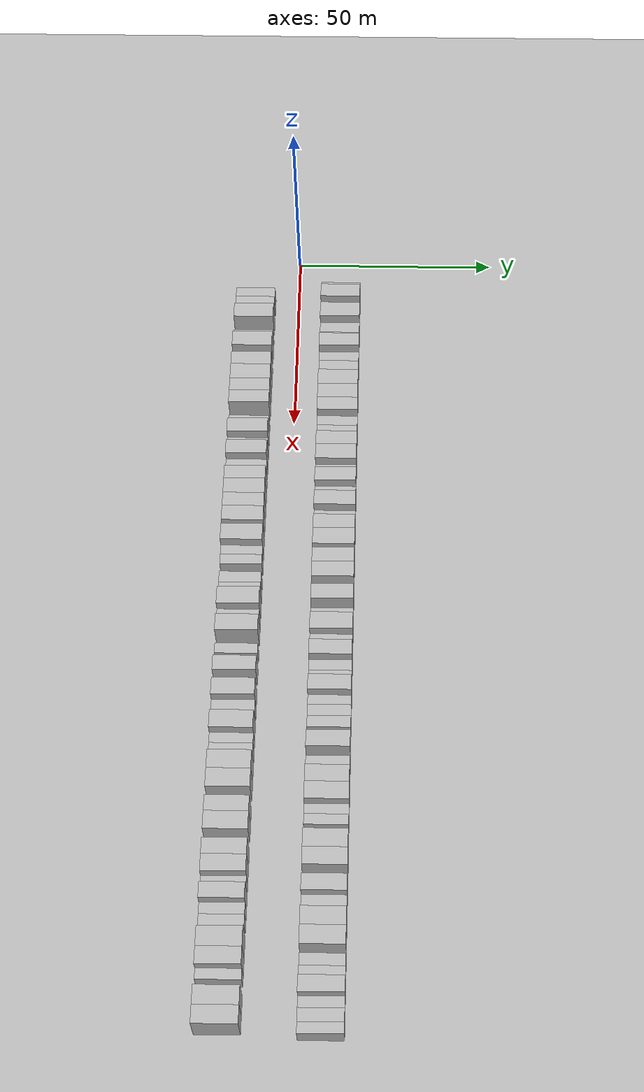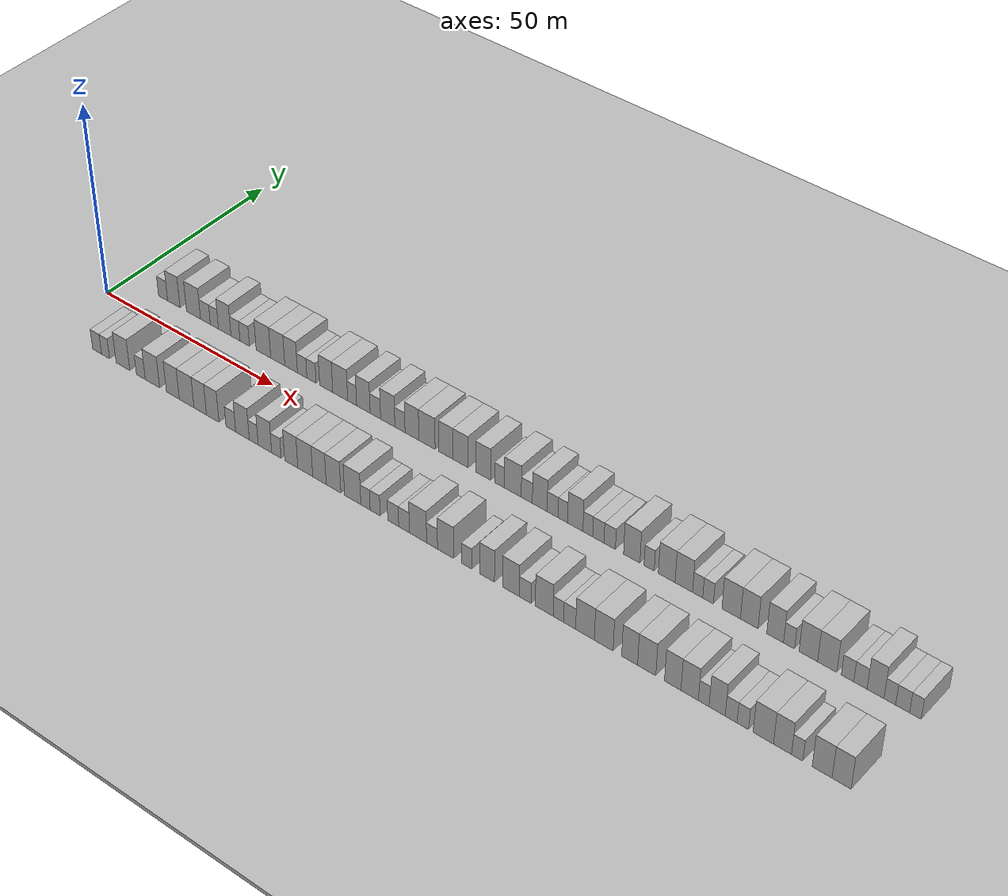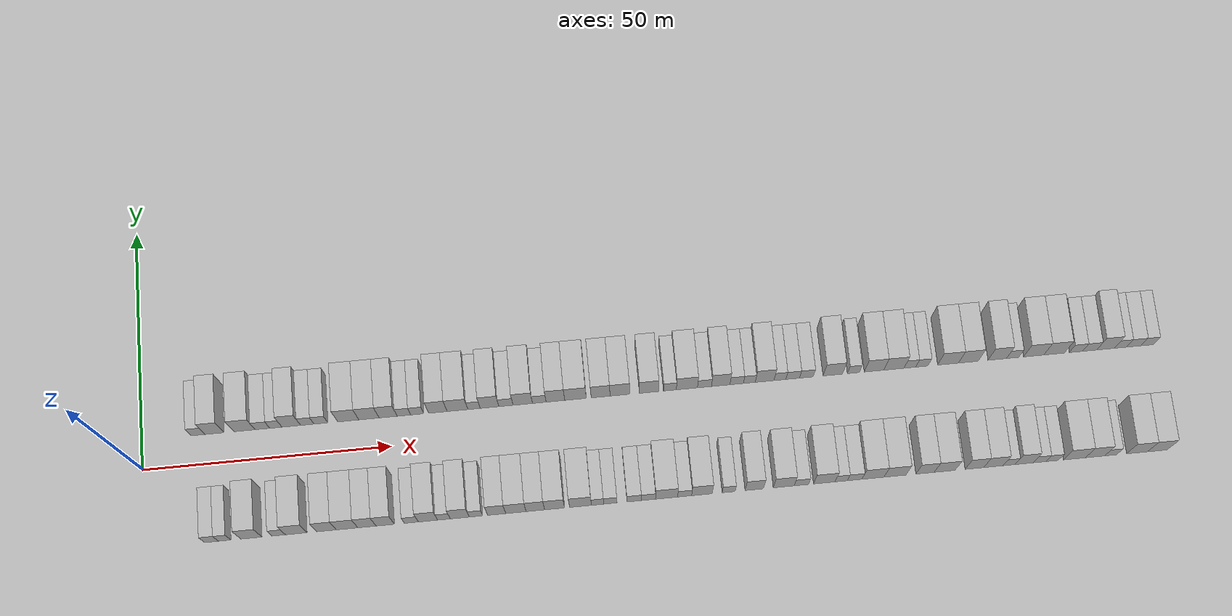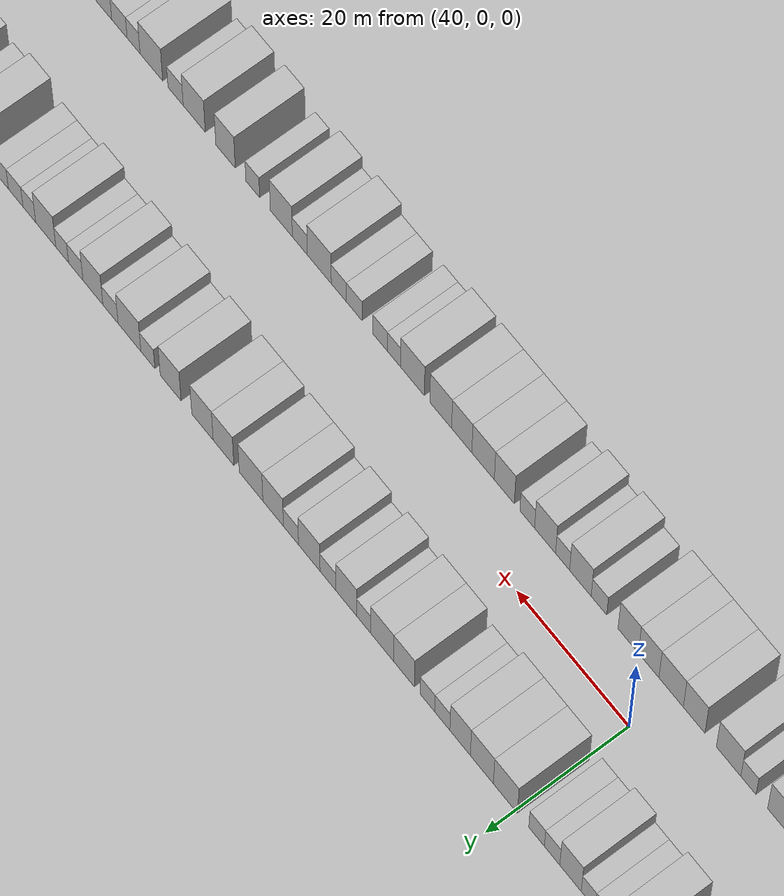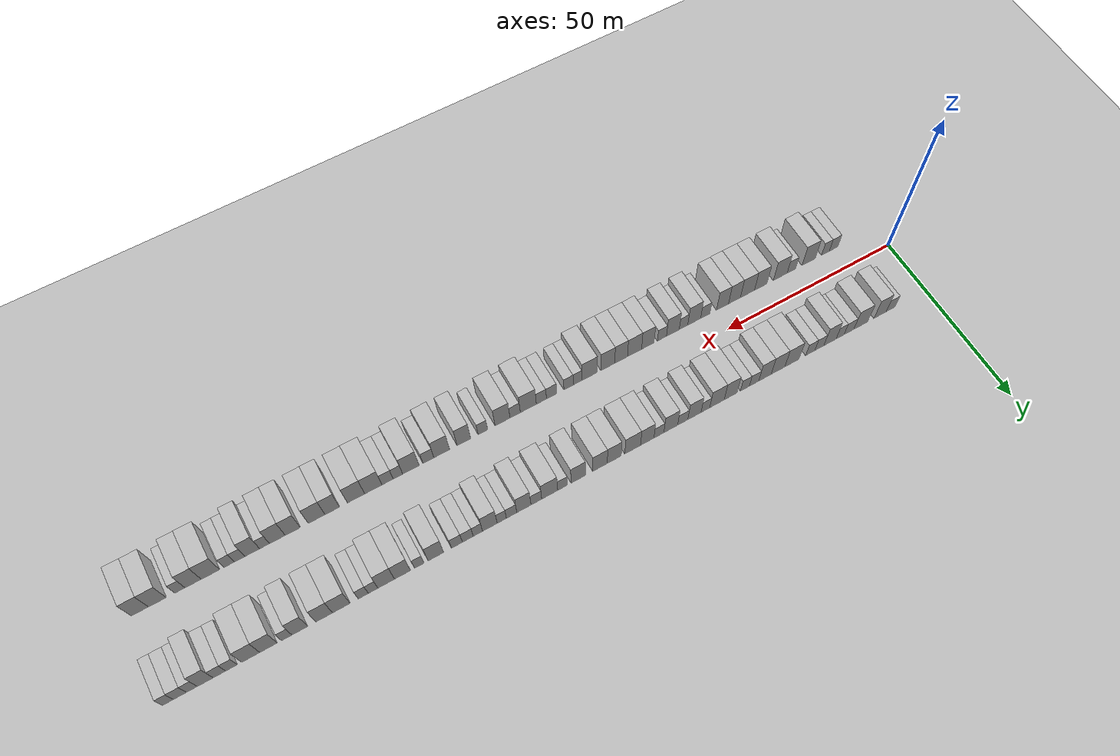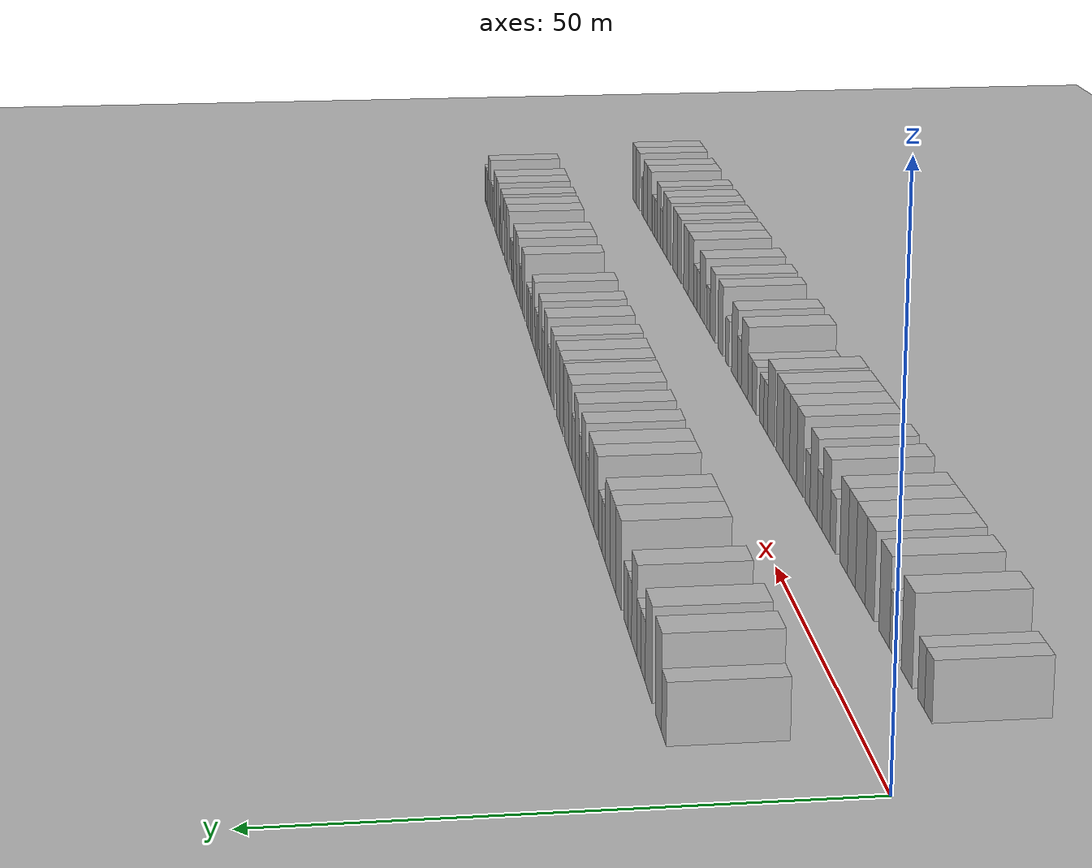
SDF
<?xml version="1.0" encoding="utf-8"?>

<sdf version="1.6">

   <world name="default">

      <gui fullscreen="0">

         <camera name="user_camera">

            <pose>-15 0 4.57585 0 0 0</pose>

            <view_controller>orbit</view_controller>

         </camera>

      </gui>

      <scene>

         <sky>

           <clouds>

             <speed>12</speed>

           </clouds>

         </sky>

         <ambient>0.4 0.4 0.4 1</ambient>

         <background>0.7 0.7 0.7 1</background>

         <shadows>1</shadows>

      </scene>

      <gravity>0 0 -9.8066</gravity>

      <magnetic_field>6e-06 2.3e-05 -4.2e-05</magnetic_field>

      <physics default="0" name="default_physics" type="ode">

         <ode>

            <solver>

               <type>quick</type>

               <iters>10</iters>

               <sor>1.0</sor>

               <use_dynamic_moi_rescaling>0</use_dynamic_moi_rescaling>

            </solver>

            <constraints>

               <cfm>0</cfm>

               <erp>0.2</erp>

               <contact_max_correcting_vel>100</contact_max_correcting_vel>

               <contact_surface_layer>0.001</contact_surface_layer>

            </constraints>

         </ode>

         <max_step_size>0.004</max_step_size>

         <real_time_factor>1</real_time_factor>

         <real_time_update_rate>250</real_time_update_rate>

      </physics>

      <light name="sun" type="directional">

         <cast_shadows>1</cast_shadows>

         <pose>0 0 10 0 0 0</pose>

         <diffuse>0.8 0.8 0.8 1</diffuse>

         <specular>0.2 0.2 0.2 1</specular>

         <attenuation>

            <range>1000</range>

            <constant>0.9</constant>

            <linear>0.01</linear>

            <quadratic>0.001</quadratic>

         </attenuation>

         <direction>-0.5 0.1 -0.9</direction>

      </light>

      <include>

         <name>ground_plane_1</name>

         <uri>model://HANNAS_ground_plane</uri>

         <pose>0 0 0  0 0 0</pose>

      </include>

      <include>

         <name>ground_plane_2</name>

         <uri>model://HANNAS_ground_plane</uri>

         <pose>100 0 0  0 0 0</pose>

      </include>

      <model name="building_1">

         <static>1</static>

         <pose frame="">11.3954 11.0000 0 0.000000 0.000000 1.570796</pose>

         <link name="link">

            <pose frame="">0 0 3.00 0 0 0</pose>

            <collision name="collision">

               <geometry>

                  <box>

                     <size>10.0000 2.7908 6.0000</size>

                  </box>

               </geometry>

               <max_contacts>10</max_contacts>

               <surface>

                  <contact>

                     <ode/>

                  </contact>

                  <bounce/>

                  <friction>

                     <torsional>

                        <ode/>

                     </torsional>

                     <ode/>

                  </friction>

               </surface>

            </collision>

            <visual name="visual">

               <cast_shadows>0</cast_shadows>

               <geometry>

                  <box>

                     <size>10.0000 2.7908 6.0000</size>

                  </box>

               </geometry>

               <material>

                  <script>

                     <uri>model://HANNAS_wall/materials/scripts</uri>

                     <uri>model://HANNAS_wall/materials/textures</uri>

                     <name>vrc/HANNAS_wall</name>

                  </script>

               </material>

            </visual>

            <self_collide>0</self_collide>

            <enable_wind>0</enable_wind>

            <kinematic>0</kinematic>

         </link>

      </model>

      <model name="building_2">

         <static>1</static>

         <pose frame="">14.7017 11.0000 0 0.000000 0.000000 1.570796</pose>

         <link name="link">

            <pose frame="">0 0 4.50 0 0 0</pose>

            <collision name="collision">

               <geometry>

                  <box>

                     <size>10.0000 3.8218 9.0000</size>

                  </box>

               </geometry>

               <max_contacts>10</max_contacts>

               <surface>

                  <contact>

                     <ode/>

                  </contact>

                  <bounce/>

                  <friction>

                     <torsional>

                        <ode/>

                     </torsional>

                     <ode/>

                  </friction>

               </surface>

            </collision>

            <visual name="visual">

               <cast_shadows>0</cast_shadows>

               <geometry>

                  <box>

                     <size>10.0000 3.8218 9.0000</size>

                  </box>

               </geometry>

               <material>

                  <script>

                     <uri>model://HANNAS_wall/materials/scripts</uri>

                     <uri>model://HANNAS_wall/materials/textures</uri>

                     <name>vrc/HANNAS_wall</name>

                  </script>

               </material>

            </visual>

            <self_collide>0</self_collide>

            <enable_wind>0</enable_wind>

            <kinematic>0</kinematic>

         </link>

      </model>

      <model name="building_3">

         <static>1</static>

         <pose frame="">20.7466 11.0000 0 0.000000 0.000000 1.570796</pose>

         <link name="link">

            <pose frame="">0 0 4.50 0 0 0</pose>

            <collision name="collision">

               <geometry>

                  <box>

                     <size>10.0000 4.2680 9.0000</size>

                  </box>

               </geometry>

               <max_contacts>10</max_contacts>

               <surface>

                  <contact>

                     <ode/>

                  </contact>

                  <bounce/>

                  <friction>

                     <torsional>

                        <ode/>

                     </torsional>

                     <ode/>

                  </friction>

               </surface>

            </collision>

            <visual name="visual">

               <cast_shadows>0</cast_shadows>

               <geometry>

                  <box>

                     <size>10.0000 4.2680 9.0000</size>

                  </box>

               </geometry>

               <material>

                  <script>

                     <uri>model://HANNAS_wall/materials/scripts</uri>

                     <uri>model://HANNAS_wall/materials/textures</uri>

                     <name>vrc/HANNAS_wall</name>

                  </script>

               </material>

            </visual>

            <self_collide>0</self_collide>

            <enable_wind>0</enable_wind>

            <kinematic>0</kinematic>

         </link>

      </model>

      <model name="building_4">

         <static>1</static>

         <pose frame="">24.3679 11.0000 0 0.000000 0.000000 1.570796</pose>

         <link name="link">

            <pose frame="">0 0 3.00 0 0 0</pose>

            <collision name="collision">

               <geometry>

                  <box>

                     <size>10.0000 2.9745 6.0000</size>

                  </box>

               </geometry>

               <max_contacts>10</max_contacts>

               <surface>

                  <contact>

                     <ode/>

                  </contact>

                  <bounce/>

                  <friction>

                     <torsional>

                        <ode/>

                     </torsional>

                     <ode/>

                  </friction>

               </surface>

            </collision>

            <visual name="visual">

               <cast_shadows>0</cast_shadows>

               <geometry>

                  <box>

                     <size>10.0000 2.9745 6.0000</size>

                  </box>

               </geometry>

               <material>

                  <script>

                     <uri>model://HANNAS_wall/materials/scripts</uri>

                     <uri>model://HANNAS_wall/materials/textures</uri>

                     <name>vrc/HANNAS_wall</name>

                  </script>

               </material>

            </visual>

            <self_collide>0</self_collide>

            <enable_wind>0</enable_wind>

            <kinematic>0</kinematic>

         </link>

      </model>

      <model name="building_5">

         <static>1</static>

         <pose frame="">27.0779 11.0000 0 0.000000 0.000000 1.570796</pose>

         <link name="link">

            <pose frame="">0 0 3.00 0 0 0</pose>

            <collision name="collision">

               <geometry>

                  <box>

                     <size>10.0000 2.4456 6.0000</size>

                  </box>

               </geometry>

               <max_contacts>10</max_contacts>

               <surface>

                  <contact>

                     <ode/>

                  </contact>

                  <bounce/>

                  <friction>

                     <torsional>

                        <ode/>

                     </torsional>

                     <ode/>

                  </friction>

               </surface>

            </collision>

            <visual name="visual">

               <cast_shadows>0</cast_shadows>

               <geometry>

                  <box>

                     <size>10.0000 2.4456 6.0000</size>

                  </box>

               </geometry>

               <material>

                  <script>

                     <uri>model://HANNAS_wall/materials/scripts</uri>

                     <uri>model://HANNAS_wall/materials/textures</uri>

                     <name>vrc/HANNAS_wall</name>

                  </script>

               </material>

            </visual>

            <self_collide>0</self_collide>

            <enable_wind>0</enable_wind>

            <kinematic>0</kinematic>

         </link>

      </model>

      <model name="building_6">

         <static>1</static>

         <pose frame="">30.1796 11.0000 0 0.000000 0.000000 1.570796</pose>

         <link name="link">

            <pose frame="">0 0 4.50 0 0 0</pose>

            <collision name="collision">

               <geometry>

                  <box>

                     <size>10.0000 3.7578 9.0000</size>

                  </box>

               </geometry>

               <max_contacts>10</max_contacts>

               <surface>

                  <contact>

                     <ode/>

                  </contact>

                  <bounce/>

                  <friction>

                     <torsional>

                        <ode/>

                     </torsional>

                     <ode/>

                  </friction>

               </surface>

            </collision>

            <visual name="visual">

               <cast_shadows>0</cast_shadows>

               <geometry>

                  <box>

                     <size>10.0000 3.7578 9.0000</size>

                  </box>

               </geometry>

               <material>

                  <script>

                     <uri>model://HANNAS_wall/materials/scripts</uri>

                     <uri>model://HANNAS_wall/materials/textures</uri>

                     <name>vrc/HANNAS_wall</name>

                  </script>

               </material>

            </visual>

            <self_collide>0</self_collide>

            <enable_wind>0</enable_wind>

            <kinematic>0</kinematic>

         </link>

      </model>

      <model name="building_7">

         <static>1</static>

         <pose frame="">33.4153 11.0000 0 0.000000 0.000000 1.570796</pose>

         <link name="link">

            <pose frame="">0 0 3.00 0 0 0</pose>

            <collision name="collision">

               <geometry>

                  <box>

                     <size>10.0000 2.7137 6.0000</size>

                  </box>

               </geometry>

               <max_contacts>10</max_contacts>

               <surface>

                  <contact>

                     <ode/>

                  </contact>

                  <bounce/>

                  <friction>

                     <torsional>

                        <ode/>

                     </torsional>

                     <ode/>

                  </friction>

               </surface>

            </collision>

            <visual name="visual">

               <cast_shadows>0</cast_shadows>

               <geometry>

                  <box>

                     <size>10.0000 2.7137 6.0000</size>

                  </box>

               </geometry>

               <material>

                  <script>

                     <uri>model://HANNAS_wall/materials/scripts</uri>

                     <uri>model://HANNAS_wall/materials/textures</uri>

                     <name>vrc/HANNAS_wall</name>

                  </script>

               </material>

            </visual>

            <self_collide>0</self_collide>

            <enable_wind>0</enable_wind>

            <kinematic>0</kinematic>

         </link>

      </model>

      <model name="building_8">

         <static>1</static>

         <pose frame="">36.1574 11.0000 0 0.000000 0.000000 1.570796</pose>

         <link name="link">

            <pose frame="">0 0 3.00 0 0 0</pose>

            <collision name="collision">

               <geometry>

                  <box>

                     <size>10.0000 2.7704 6.0000</size>

                  </box>

               </geometry>

               <max_contacts>10</max_contacts>

               <surface>

                  <contact>

                     <ode/>

                  </contact>

                  <bounce/>

                  <friction>

                     <torsional>

                        <ode/>

                     </torsional>

                     <ode/>

                  </friction>

               </surface>

            </collision>

            <visual name="visual">

               <cast_shadows>0</cast_shadows>

               <geometry>

                  <box>

                     <size>10.0000 2.7704 6.0000</size>

                  </box>

               </geometry>

               <material>

                  <script>

                     <uri>model://HANNAS_wall/materials/scripts</uri>

                     <uri>model://HANNAS_wall/materials/textures</uri>

                     <name>vrc/HANNAS_wall</name>

                  </script>

               </material>

            </visual>

            <self_collide>0</self_collide>

            <enable_wind>0</enable_wind>

            <kinematic>0</kinematic>

         </link>

      </model>

      <model name="building_9">

         <static>1</static>

         <pose frame="">41.6793 11.0000 0 0.000000 0.000000 1.570796</pose>

         <link name="link">

            <pose frame="">0 0 4.50 0 0 0</pose>

            <collision name="collision">

               <geometry>

                  <box>

                     <size>10.0000 4.2735 9.0000</size>

                  </box>

               </geometry>

               <max_contacts>10</max_contacts>

               <surface>

                  <contact>

                     <ode/>

                  </contact>

                  <bounce/>

                  <friction>

                     <torsional>

                        <ode/>

                     </torsional>

                     <ode/>

                  </friction>

               </surface>

            </collision>

            <visual name="visual">

               <cast_shadows>0</cast_shadows>

               <geometry>

                  <box>

                     <size>10.0000 4.2735 9.0000</size>

                  </box>

               </geometry>

               <material>

                  <script>

                     <uri>model://HANNAS_wall/materials/scripts</uri>

                     <uri>model://HANNAS_wall/materials/textures</uri>

                     <name>vrc/HANNAS_wall</name>

                  </script>

               </material>

            </visual>

            <self_collide>0</self_collide>

            <enable_wind>0</enable_wind>

            <kinematic>0</kinematic>

         </link>

      </model>

      <model name="building_10">

         <static>1</static>

         <pose frame="">45.8695 11.0000 0 0.000000 0.000000 1.570796</pose>

         <link name="link">

            <pose frame="">0 0 4.50 0 0 0</pose>

            <collision name="collision">

               <geometry>

                  <box>

                     <size>10.0000 4.1068 9.0000</size>

                  </box>

               </geometry>

               <max_contacts>10</max_contacts>

               <surface>

                  <contact>

                     <ode/>

                  </contact>

                  <bounce/>

                  <friction>

                     <torsional>

                        <ode/>

                     </torsional>

                     <ode/>

                  </friction>

               </surface>

            </collision>

            <visual name="visual">

               <cast_shadows>0</cast_shadows>

               <geometry>

                  <box>

                     <size>10.0000 4.1068 9.0000</size>

                  </box>

               </geometry>

               <material>

                  <script>

                     <uri>model://HANNAS_wall/materials/scripts</uri>

                     <uri>model://HANNAS_wall/materials/textures</uri>

                     <name>vrc/HANNAS_wall</name>

                  </script>

               </material>

            </visual>

            <self_collide>0</self_collide>

            <enable_wind>0</enable_wind>

            <kinematic>0</kinematic>

         </link>

      </model>

      <model name="building_11">

         <static>1</static>

         <pose frame="">49.7489 11.0000 0 0.000000 0.000000 1.570796</pose>

         <link name="link">

            <pose frame="">0 0 4.50 0 0 0</pose>

            <collision name="collision">

               <geometry>

                  <box>

                     <size>10.0000 3.6519 9.0000</size>

                  </box>

               </geometry>

               <max_contacts>10</max_contacts>

               <surface>

                  <contact>

                     <ode/>

                  </contact>

                  <bounce/>

                  <friction>

                     <torsional>

                        <ode/>

                     </torsional>

                     <ode/>

                  </friction>

               </surface>

            </collision>

            <visual name="visual">

               <cast_shadows>0</cast_shadows>

               <geometry>

                  <box>

                     <size>10.0000 3.6519 9.0000</size>

                  </box>

               </geometry>

               <material>

                  <script>

                     <uri>model://HANNAS_wall/materials/scripts</uri>

                     <uri>model://HANNAS_wall/materials/textures</uri>

                     <name>vrc/HANNAS_wall</name>

                  </script>

               </material>

            </visual>

            <self_collide>0</self_collide>

            <enable_wind>0</enable_wind>

            <kinematic>0</kinematic>

         </link>

      </model>

      <model name="building_12">

         <static>1</static>

         <pose frame="">52.9385 11.0000 0 0.000000 0.000000 1.570796</pose>

         <link name="link">

            <pose frame="">0 0 3.00 0 0 0</pose>

            <collision name="collision">

               <geometry>

                  <box>

                     <size>10.0000 2.7273 6.0000</size>

                  </box>

               </geometry>

               <max_contacts>10</max_contacts>

               <surface>

                  <contact>

                     <ode/>

                  </contact>

                  <bounce/>

                  <friction>

                     <torsional>

                        <ode/>

                     </torsional>

                     <ode/>

                  </friction>

               </surface>

            </collision>

            <visual name="visual">

               <cast_shadows>0</cast_shadows>

               <geometry>

                  <box>

                     <size>10.0000 2.7273 6.0000</size>

                  </box>

               </geometry>

               <material>

                  <script>

                     <uri>model://HANNAS_wall/materials/scripts</uri>

                     <uri>model://HANNAS_wall/materials/textures</uri>

                     <name>vrc/HANNAS_wall</name>

                  </script>

               </material>

            </visual>

            <self_collide>0</self_collide>

            <enable_wind>0</enable_wind>

            <kinematic>0</kinematic>

         </link>

      </model>

      <model name="building_13">

         <static>1</static>

         <pose frame="">55.6224 11.0000 0 0.000000 0.000000 1.570796</pose>

         <link name="link">

            <pose frame="">0 0 3.00 0 0 0</pose>

            <collision name="collision">

               <geometry>

                  <box>

                     <size>10.0000 2.6405 6.0000</size>

                  </box>

               </geometry>

               <max_contacts>10</max_contacts>

               <surface>

                  <contact>

                     <ode/>

                  </contact>

                  <bounce/>

                  <friction>

                     <torsional>

                        <ode/>

                     </torsional>

                     <ode/>

                  </friction>

               </surface>

            </collision>

            <visual name="visual">

               <cast_shadows>0</cast_shadows>

               <geometry>

                  <box>

                     <size>10.0000 2.6405 6.0000</size>

                  </box>

               </geometry>

               <material>

                  <script>

                     <uri>model://HANNAS_wall/materials/scripts</uri>

                     <uri>model://HANNAS_wall/materials/textures</uri>

                     <name>vrc/HANNAS_wall</name>

                  </script>

               </material>

            </visual>

            <self_collide>0</self_collide>

            <enable_wind>0</enable_wind>

            <kinematic>0</kinematic>

         </link>

      </model>

      <model name="building_14">

         <static>1</static>

         <pose frame="">59.8101 11.0000 0 0.000000 0.000000 1.570796</pose>

         <link name="link">

            <pose frame="">0 0 4.50 0 0 0</pose>

            <collision name="collision">

               <geometry>

                  <box>

                     <size>10.0000 3.7348 9.0000</size>

                  </box>

               </geometry>

               <max_contacts>10</max_contacts>

               <surface>

                  <contact>

                     <ode/>

                  </contact>

                  <bounce/>

                  <friction>

                     <torsional>

                        <ode/>

                     </torsional>

                     <ode/>

                  </friction>

               </surface>

            </collision>

            <visual name="visual">

               <cast_shadows>0</cast_shadows>

               <geometry>

                  <box>

                     <size>10.0000 3.7348 9.0000</size>

                  </box>

               </geometry>

               <material>

                  <script>

                     <uri>model://HANNAS_wall/materials/scripts</uri>

                     <uri>model://HANNAS_wall/materials/textures</uri>

                     <name>vrc/HANNAS_wall</name>

                  </script>

               </material>

            </visual>

            <self_collide>0</self_collide>

            <enable_wind>0</enable_wind>

            <kinematic>0</kinematic>

         </link>

      </model>

      <model name="building_15">

         <static>1</static>

         <pose frame="">63.7814 11.0000 0 0.000000 0.000000 1.570796</pose>

         <link name="link">

            <pose frame="">0 0 4.50 0 0 0</pose>

            <collision name="collision">

               <geometry>

                  <box>

                     <size>10.0000 4.2078 9.0000</size>

                  </box>

               </geometry>

               <max_contacts>10</max_contacts>

               <surface>

                  <contact>

                     <ode/>

                  </contact>

                  <bounce/>

                  <friction>

                     <torsional>

                        <ode/>

                     </torsional>

                     <ode/>

                  </friction>

               </surface>

            </collision>

            <visual name="visual">

               <cast_shadows>0</cast_shadows>

               <geometry>

                  <box>

                     <size>10.0000 4.2078 9.0000</size>

                  </box>

               </geometry>

               <material>

                  <script>

                     <uri>model://HANNAS_wall/materials/scripts</uri>

                     <uri>model://HANNAS_wall/materials/textures</uri>

                     <name>vrc/HANNAS_wall</name>

                  </script>

               </material>

            </visual>

            <self_collide>0</self_collide>

            <enable_wind>0</enable_wind>

            <kinematic>0</kinematic>

         </link>

      </model>

      <model name="building_16">

         <static>1</static>

         <pose frame="">67.1311 11.0000 0 0.000000 0.000000 1.570796</pose>

         <link name="link">

            <pose frame="">0 0 3.00 0 0 0</pose>

            <collision name="collision">

               <geometry>

                  <box>

                     <size>10.0000 2.4916 6.0000</size>

                  </box>

               </geometry>

               <max_contacts>10</max_contacts>

               <surface>

                  <contact>

                     <ode/>

                  </contact>

                  <bounce/>

                  <friction>

                     <torsional>

                        <ode/>

                     </torsional>

                     <ode/>

                  </friction>

               </surface>

            </collision>

            <visual name="visual">

               <cast_shadows>0</cast_shadows>

               <geometry>

                  <box>

                     <size>10.0000 2.4916 6.0000</size>

                  </box>

               </geometry>

               <material>

                  <script>

                     <uri>model://HANNAS_wall/materials/scripts</uri>

                     <uri>model://HANNAS_wall/materials/textures</uri>

                     <name>vrc/HANNAS_wall</name>

                  </script>

               </material>

            </visual>

            <self_collide>0</self_collide>

            <enable_wind>0</enable_wind>

            <kinematic>0</kinematic>

         </link>

      </model>

      <model name="building_17">

         <static>1</static>

         <pose frame="">70.2691 11.0000 0 0.000000 0.000000 1.570796</pose>

         <link name="link">

            <pose frame="">0 0 4.50 0 0 0</pose>

            <collision name="collision">

               <geometry>

                  <box>

                     <size>10.0000 3.7843 9.0000</size>

                  </box>

               </geometry>

               <max_contacts>10</max_contacts>

               <surface>

                  <contact>

                     <ode/>

                  </contact>

                  <bounce/>

                  <friction>

                     <torsional>

                        <ode/>

                     </torsional>

                     <ode/>

                  </friction>

               </surface>

            </collision>

            <visual name="visual">

               <cast_shadows>0</cast_shadows>

               <geometry>

                  <box>

                     <size>10.0000 3.7843 9.0000</size>

                  </box>

               </geometry>

               <material>

                  <script>

                     <uri>model://HANNAS_wall/materials/scripts</uri>

                     <uri>model://HANNAS_wall/materials/textures</uri>

                     <name>vrc/HANNAS_wall</name>

                  </script>

               </material>

            </visual>

            <self_collide>0</self_collide>

            <enable_wind>0</enable_wind>

            <kinematic>0</kinematic>

         </link>

      </model>

      <model name="building_18">

         <static>1</static>

         <pose frame="">73.6063 11.0000 0 0.000000 0.000000 1.570796</pose>

         <link name="link">

            <pose frame="">0 0 3.00 0 0 0</pose>

            <collision name="collision">

               <geometry>

                  <box>

                     <size>10.0000 2.8903 6.0000</size>

                  </box>

               </geometry>

               <max_contacts>10</max_contacts>

               <surface>

                  <contact>

                     <ode/>

                  </contact>

                  <bounce/>

                  <friction>

                     <torsional>

                        <ode/>

                     </torsional>

                     <ode/>

                  </friction>

               </surface>

            </collision>

            <visual name="visual">

               <cast_shadows>0</cast_shadows>

               <geometry>

                  <box>

                     <size>10.0000 2.8903 6.0000</size>

                  </box>

               </geometry>

               <material>

                  <script>

                     <uri>model://HANNAS_wall/materials/scripts</uri>

                     <uri>model://HANNAS_wall/materials/textures</uri>

                     <name>vrc/HANNAS_wall</name>

                  </script>

               </material>

            </visual>

            <self_collide>0</self_collide>

            <enable_wind>0</enable_wind>

            <kinematic>0</kinematic>

         </link>

      </model>

      <model name="building_19">

         <static>1</static>

         <pose frame="">77.0199 11.0000 0 0.000000 0.000000 1.570796</pose>

         <link name="link">

            <pose frame="">0 0 4.50 0 0 0</pose>

            <collision name="collision">

               <geometry>

                  <box>

                     <size>10.0000 3.9369 9.0000</size>

                  </box>

               </geometry>

               <max_contacts>10</max_contacts>

               <surface>

                  <contact>

                     <ode/>

                  </contact>

                  <bounce/>

                  <friction>

                     <torsional>

                        <ode/>

                     </torsional>

                     <ode/>

                  </friction>

               </surface>

            </collision>

            <visual name="visual">

               <cast_shadows>0</cast_shadows>

               <geometry>

                  <box>

                     <size>10.0000 3.9369 9.0000</size>

                  </box>

               </geometry>

               <material>

                  <script>

                     <uri>model://HANNAS_wall/materials/scripts</uri>

                     <uri>model://HANNAS_wall/materials/textures</uri>

                     <name>vrc/HANNAS_wall</name>

                  </script>

               </material>

            </visual>

            <self_collide>0</self_collide>

            <enable_wind>0</enable_wind>

            <kinematic>0</kinematic>

         </link>

      </model>

      <model name="building_20">

         <static>1</static>

         <pose frame="">80.3726 11.0000 0 0.000000 0.000000 1.570796</pose>

         <link name="link">

            <pose frame="">0 0 3.00 0 0 0</pose>

            <collision name="collision">

               <geometry>

                  <box>

                     <size>10.0000 2.7685 6.0000</size>

                  </box>

               </geometry>

               <max_contacts>10</max_contacts>

               <surface>

                  <contact>

                     <ode/>

                  </contact>

                  <bounce/>

                  <friction>

                     <torsional>

                        <ode/>

                     </torsional>

                     <ode/>

                  </friction>

               </surface>

            </collision>

            <visual name="visual">

               <cast_shadows>0</cast_shadows>

               <geometry>

                  <box>

                     <size>10.0000 2.7685 6.0000</size>

                  </box>

               </geometry>

               <material>

                  <script>

                     <uri>model://HANNAS_wall/materials/scripts</uri>

                     <uri>model://HANNAS_wall/materials/textures</uri>

                     <name>vrc/HANNAS_wall</name>

                  </script>

               </material>

            </visual>

            <self_collide>0</self_collide>

            <enable_wind>0</enable_wind>

            <kinematic>0</kinematic>

         </link>

      </model>

      <model name="building_21">

         <static>1</static>

         <pose frame="">83.6464 11.0000 0 0.000000 0.000000 1.570796</pose>

         <link name="link">

            <pose frame="">0 0 4.50 0 0 0</pose>

            <collision name="collision">

               <geometry>

                  <box>

                     <size>10.0000 3.7791 9.0000</size>

                  </box>

               </geometry>

               <max_contacts>10</max_contacts>

               <surface>

                  <contact>

                     <ode/>

                  </contact>

                  <bounce/>

                  <friction>

                     <torsional>

                        <ode/>

                     </torsional>

                     <ode/>

                  </friction>

               </surface>

            </collision>

            <visual name="visual">

               <cast_shadows>0</cast_shadows>

               <geometry>

                  <box>

                     <size>10.0000 3.7791 9.0000</size>

                  </box>

               </geometry>

               <material>

                  <script>

                     <uri>model://HANNAS_wall/materials/scripts</uri>

                     <uri>model://HANNAS_wall/materials/textures</uri>

                     <name>vrc/HANNAS_wall</name>

                  </script>

               </material>

            </visual>

            <self_collide>0</self_collide>

            <enable_wind>0</enable_wind>

            <kinematic>0</kinematic>

         </link>

      </model>

      <model name="building_22">

         <static>1</static>

         <pose frame="">87.7189 11.0000 0 0.000000 0.000000 1.570796</pose>

         <link name="link">

            <pose frame="">0 0 4.50 0 0 0</pose>

            <collision name="collision">

               <geometry>

                  <box>

                     <size>10.0000 4.3659 9.0000</size>

                  </box>

               </geometry>

               <max_contacts>10</max_contacts>

               <surface>

                  <contact>

                     <ode/>

                  </contact>

                  <bounce/>

                  <friction>

                     <torsional>

                        <ode/>

                     </torsional>

                     <ode/>

                  </friction>

               </surface>

            </collision>

            <visual name="visual">

               <cast_shadows>0</cast_shadows>

               <geometry>

                  <box>

                     <size>10.0000 4.3659 9.0000</size>

                  </box>

               </geometry>

               <material>

                  <script>

                     <uri>model://HANNAS_wall/materials/scripts</uri>

                     <uri>model://HANNAS_wall/materials/textures</uri>

                     <name>vrc/HANNAS_wall</name>

                  </script>

               </material>

            </visual>

            <self_collide>0</self_collide>

            <enable_wind>0</enable_wind>

            <kinematic>0</kinematic>

         </link>

      </model>

      <model name="building_23">

         <static>1</static>

         <pose frame="">92.8211 11.0000 0 0.000000 0.000000 1.570796</pose>

         <link name="link">

            <pose frame="">0 0 4.50 0 0 0</pose>

            <collision name="collision">

               <geometry>

                  <box>

                     <size>10.0000 3.8386 9.0000</size>

                  </box>

               </geometry>

               <max_contacts>10</max_contacts>

               <surface>

                  <contact>

                     <ode/>

                  </contact>

                  <bounce/>

                  <friction>

                     <torsional>

                        <ode/>

                     </torsional>

                     <ode/>

                  </friction>

               </surface>

            </collision>

            <visual name="visual">

               <cast_shadows>0</cast_shadows>

               <geometry>

                  <box>

                     <size>10.0000 3.8386 9.0000</size>

                  </box>

               </geometry>

               <material>

                  <script>

                     <uri>model://HANNAS_wall/materials/scripts</uri>

                     <uri>model://HANNAS_wall/materials/textures</uri>

                     <name>vrc/HANNAS_wall</name>

                  </script>

               </material>

            </visual>

            <self_collide>0</self_collide>

            <enable_wind>0</enable_wind>

            <kinematic>0</kinematic>

         </link>

      </model>

      <model name="building_24">

         <static>1</static>

         <pose frame="">96.7313 11.0000 0 0.000000 0.000000 1.570796</pose>

         <link name="link">

            <pose frame="">0 0 4.50 0 0 0</pose>

            <collision name="collision">

               <geometry>

                  <box>

                     <size>10.0000 3.9817 9.0000</size>

                  </box>

               </geometry>

               <max_contacts>10</max_contacts>

               <surface>

                  <contact>

                     <ode/>

                  </contact>

                  <bounce/>

                  <friction>

                     <torsional>

                        <ode/>

                     </torsional>

                     <ode/>

                  </friction>

               </surface>

            </collision>

            <visual name="visual">

               <cast_shadows>0</cast_shadows>

               <geometry>

                  <box>

                     <size>10.0000 3.9817 9.0000</size>

                  </box>

               </geometry>

               <material>

                  <script>

                     <uri>model://HANNAS_wall/materials/scripts</uri>

                     <uri>model://HANNAS_wall/materials/textures</uri>

                     <name>vrc/HANNAS_wall</name>

                  </script>

               </material>

            </visual>

            <self_collide>0</self_collide>

            <enable_wind>0</enable_wind>

            <kinematic>0</kinematic>

         </link>

      </model>

      <model name="building_25">

         <static>1</static>

         <pose frame="">102.6719 11.0000 0 0.000000 0.000000 1.570796</pose>

         <link name="link">

            <pose frame="">0 0 4.50 0 0 0</pose>

            <collision name="collision">

               <geometry>

                  <box>

                     <size>10.0000 3.8996 9.0000</size>

                  </box>

               </geometry>

               <max_contacts>10</max_contacts>

               <surface>

                  <contact>

                     <ode/>

                  </contact>

                  <bounce/>

                  <friction>

                     <torsional>

                        <ode/>

                     </torsional>

                     <ode/>

                  </friction>

               </surface>

            </collision>

            <visual name="visual">

               <cast_shadows>0</cast_shadows>

               <geometry>

                  <box>

                     <size>10.0000 3.8996 9.0000</size>

                  </box>

               </geometry>

               <material>

                  <script>

                     <uri>model://HANNAS_wall/materials/scripts</uri>

                     <uri>model://HANNAS_wall/materials/textures</uri>

                     <name>vrc/HANNAS_wall</name>

                  </script>

               </material>

            </visual>

            <self_collide>0</self_collide>

            <enable_wind>0</enable_wind>

            <kinematic>0</kinematic>

         </link>

      </model>

      <model name="building_26">

         <static>1</static>

         <pose frame="">106.9295 11.0000 0 0.000000 0.000000 1.570796</pose>

         <link name="link">

            <pose frame="">0 0 3.00 0 0 0</pose>

            <collision name="collision">

               <geometry>

                  <box>

                     <size>10.0000 2.6156 6.0000</size>

                  </box>

               </geometry>

               <max_contacts>10</max_contacts>

               <surface>

                  <contact>

                     <ode/>

                  </contact>

                  <bounce/>

                  <friction>

                     <torsional>

                        <ode/>

                     </torsional>

                     <ode/>

                  </friction>

               </surface>

            </collision>

            <visual name="visual">

               <cast_shadows>0</cast_shadows>

               <geometry>

                  <box>

                     <size>10.0000 2.6156 6.0000</size>

                  </box>

               </geometry>

               <material>

                  <script>

                     <uri>model://HANNAS_wall/materials/scripts</uri>

                     <uri>model://HANNAS_wall/materials/textures</uri>

                     <name>vrc/HANNAS_wall</name>

                  </script>

               </material>

            </visual>

            <self_collide>0</self_collide>

            <enable_wind>0</enable_wind>

            <kinematic>0</kinematic>

         </link>

      </model>

      <model name="building_27">

         <static>1</static>

         <pose frame="">110.3880 11.0000 0 0.000000 0.000000 1.570796</pose>

         <link name="link">

            <pose frame="">0 0 4.50 0 0 0</pose>

            <collision name="collision">

               <geometry>

                  <box>

                     <size>10.0000 4.3013 9.0000</size>

                  </box>

               </geometry>

               <max_contacts>10</max_contacts>

               <surface>

                  <contact>

                     <ode/>

                  </contact>

                  <bounce/>

                  <friction>

                     <torsional>

                        <ode/>

                     </torsional>

                     <ode/>

                  </friction>

               </surface>

            </collision>

            <visual name="visual">

               <cast_shadows>0</cast_shadows>

               <geometry>

                  <box>

                     <size>10.0000 4.3013 9.0000</size>

                  </box>

               </geometry>

               <material>

                  <script>

                     <uri>model://HANNAS_wall/materials/scripts</uri>

                     <uri>model://HANNAS_wall/materials/textures</uri>

                     <name>vrc/HANNAS_wall</name>

                  </script>

               </material>

            </visual>

            <self_collide>0</self_collide>

            <enable_wind>0</enable_wind>

            <kinematic>0</kinematic>

         </link>

      </model>

      <model name="building_28">

         <static>1</static>

         <pose frame="">113.9667 11.0000 0 0.000000 0.000000 1.570796</pose>

         <link name="link">

            <pose frame="">0 0 3.00 0 0 0</pose>

            <collision name="collision">

               <geometry>

                  <box>

                     <size>10.0000 2.8562 6.0000</size>

                  </box>

               </geometry>

               <max_contacts>10</max_contacts>

               <surface>

                  <contact>

                     <ode/>

                  </contact>

                  <bounce/>

                  <friction>

                     <torsional>

                        <ode/>

                     </torsional>

                     <ode/>

                  </friction>

               </surface>

            </collision>

            <visual name="visual">

               <cast_shadows>0</cast_shadows>

               <geometry>

                  <box>

                     <size>10.0000 2.8562 6.0000</size>

                  </box>

               </geometry>

               <material>

                  <script>

                     <uri>model://HANNAS_wall/materials/scripts</uri>

                     <uri>model://HANNAS_wall/materials/textures</uri>

                     <name>vrc/HANNAS_wall</name>

                  </script>

               </material>

            </visual>

            <self_collide>0</self_collide>

            <enable_wind>0</enable_wind>

            <kinematic>0</kinematic>

         </link>

      </model>

      <model name="building_29">

         <static>1</static>

         <pose frame="">117.2774 11.0000 0 0.000000 0.000000 1.570796</pose>

         <link name="link">

            <pose frame="">0 0 4.50 0 0 0</pose>

            <collision name="collision">

               <geometry>

                  <box>

                     <size>10.0000 3.7653 9.0000</size>

                  </box>

               </geometry>

               <max_contacts>10</max_contacts>

               <surface>

                  <contact>

                     <ode/>

                  </contact>

                  <bounce/>

                  <friction>

                     <torsional>

                        <ode/>

                     </torsional>

                     <ode/>

                  </friction>

               </surface>

            </collision>

            <visual name="visual">

               <cast_shadows>0</cast_shadows>

               <geometry>

                  <box>

                     <size>10.0000 3.7653 9.0000</size>

                  </box>

               </geometry>

               <material>

                  <script>

                     <uri>model://HANNAS_wall/materials/scripts</uri>

                     <uri>model://HANNAS_wall/materials/textures</uri>

                     <name>vrc/HANNAS_wall</name>

                  </script>

               </material>

            </visual>

            <self_collide>0</self_collide>

            <enable_wind>0</enable_wind>

            <kinematic>0</kinematic>

         </link>

      </model>

      <model name="building_30">

         <static>1</static>

         <pose frame="">120.5377 11.0000 0 0.000000 0.000000 1.570796</pose>

         <link name="link">

            <pose frame="">0 0 3.00 0 0 0</pose>

            <collision name="collision">

               <geometry>

                  <box>

                     <size>10.0000 2.7552 6.0000</size>

                  </box>

               </geometry>

               <max_contacts>10</max_contacts>

               <surface>

                  <contact>

                     <ode/>

                  </contact>

                  <bounce/>

                  <friction>

                     <torsional>

                        <ode/>

                     </torsional>

                     <ode/>

                  </friction>

               </surface>

            </collision>

            <visual name="visual">

               <cast_shadows>0</cast_shadows>

               <geometry>

                  <box>

                     <size>10.0000 2.7552 6.0000</size>

                  </box>

               </geometry>

               <material>

                  <script>

                     <uri>model://HANNAS_wall/materials/scripts</uri>

                     <uri>model://HANNAS_wall/materials/textures</uri>

                     <name>vrc/HANNAS_wall</name>

                  </script>

               </material>

            </visual>

            <self_collide>0</self_collide>

            <enable_wind>0</enable_wind>

            <kinematic>0</kinematic>

         </link>

      </model>

      <model name="building_31">

         <static>1</static>

         <pose frame="">123.1191 11.0000 0 0.000000 0.000000 1.570796</pose>

         <link name="link">

            <pose frame="">0 0 3.00 0 0 0</pose>

            <collision name="collision">

               <geometry>

                  <box>

                     <size>10.0000 2.4076 6.0000</size>

                  </box>

               </geometry>

               <max_contacts>10</max_contacts>

               <surface>

                  <contact>

                     <ode/>

                  </contact>

                  <bounce/>

                  <friction>

                     <torsional>

                        <ode/>

                     </torsional>

                     <ode/>

                  </friction>

               </surface>

            </collision>

            <visual name="visual">

               <cast_shadows>0</cast_shadows>

               <geometry>

                  <box>

                     <size>10.0000 2.4076 6.0000</size>

                  </box>

               </geometry>

               <material>

                  <script>

                     <uri>model://HANNAS_wall/materials/scripts</uri>

                     <uri>model://HANNAS_wall/materials/textures</uri>

                     <name>vrc/HANNAS_wall</name>

                  </script>

               </material>

            </visual>

            <self_collide>0</self_collide>

            <enable_wind>0</enable_wind>

            <kinematic>0</kinematic>

         </link>

      </model>

      <model name="building_32">

         <static>1</static>

         <pose frame="">126.2458 11.0000 0 0.000000 0.000000 1.570796</pose>

         <link name="link">

            <pose frame="">0 0 4.50 0 0 0</pose>

            <collision name="collision">

               <geometry>

                  <box>

                     <size>10.0000 3.8459 9.0000</size>

                  </box>

               </geometry>

               <max_contacts>10</max_contacts>

               <surface>

                  <contact>

                     <ode/>

                  </contact>

                  <bounce/>

                  <friction>

                     <torsional>

                        <ode/>

                     </torsional>

                     <ode/>

                  </friction>

               </surface>

            </collision>

            <visual name="visual">

               <cast_shadows>0</cast_shadows>

               <geometry>

                  <box>

                     <size>10.0000 3.8459 9.0000</size>

                  </box>

               </geometry>

               <material>

                  <script>

                     <uri>model://HANNAS_wall/materials/scripts</uri>

                     <uri>model://HANNAS_wall/materials/textures</uri>

                     <name>vrc/HANNAS_wall</name>

                  </script>

               </material>

            </visual>

            <self_collide>0</self_collide>

            <enable_wind>0</enable_wind>

            <kinematic>0</kinematic>

         </link>

      </model>

      <model name="building_33">

         <static>1</static>

         <pose frame="">129.3854 11.0000 0 0.000000 0.000000 1.570796</pose>

         <link name="link">

            <pose frame="">0 0 3.00 0 0 0</pose>

            <collision name="collision">

               <geometry>

                  <box>

                     <size>10.0000 2.4332 6.0000</size>

                  </box>

               </geometry>

               <max_contacts>10</max_contacts>

               <surface>

                  <contact>

                     <ode/>

                  </contact>

                  <bounce/>

                  <friction>

                     <torsional>

                        <ode/>

                     </torsional>

                     <ode/>

                  </friction>

               </surface>

            </collision>

            <visual name="visual">

               <cast_shadows>0</cast_shadows>

               <geometry>

                  <box>

                     <size>10.0000 2.4332 6.0000</size>

                  </box>

               </geometry>

               <material>

                  <script>

                     <uri>model://HANNAS_wall/materials/scripts</uri>

                     <uri>model://HANNAS_wall/materials/textures</uri>

                     <name>vrc/HANNAS_wall</name>

                  </script>

               </material>

            </visual>

            <self_collide>0</self_collide>

            <enable_wind>0</enable_wind>

            <kinematic>0</kinematic>

         </link>

      </model>

      <model name="building_34">

         <static>1</static>

         <pose frame="">131.9970 11.0000 0 0.000000 0.000000 1.570796</pose>

         <link name="link">

            <pose frame="">0 0 3.00 0 0 0</pose>

            <collision name="collision">

               <geometry>

                  <box>

                     <size>10.0000 2.7901 6.0000</size>

                  </box>

               </geometry>

               <max_contacts>10</max_contacts>

               <surface>

                  <contact>

                     <ode/>

                  </contact>

                  <bounce/>

                  <friction>

                     <torsional>

                        <ode/>

                     </torsional>

                     <ode/>

                  </friction>

               </surface>

            </collision>

            <visual name="visual">

               <cast_shadows>0</cast_shadows>

               <geometry>

                  <box>

                     <size>10.0000 2.7901 6.0000</size>

                  </box>

               </geometry>

               <material>

                  <script>

                     <uri>model://HANNAS_wall/materials/scripts</uri>

                     <uri>model://HANNAS_wall/materials/textures</uri>

                     <name>vrc/HANNAS_wall</name>

                  </script>

               </material>

            </visual>

            <self_collide>0</self_collide>

            <enable_wind>0</enable_wind>

            <kinematic>0</kinematic>

         </link>

      </model>

      <model name="building_35">

         <static>1</static>

         <pose frame="">134.8009 11.0000 0 0.000000 0.000000 1.570796</pose>

         <link name="link">

            <pose frame="">0 0 3.00 0 0 0</pose>

            <collision name="collision">

               <geometry>

                  <box>

                     <size>10.0000 2.8178 6.0000</size>

                  </box>

               </geometry>

               <max_contacts>10</max_contacts>

               <surface>

                  <contact>

                     <ode/>

                  </contact>

                  <bounce/>

                  <friction>

                     <torsional>

                        <ode/>

                     </torsional>

                     <ode/>

                  </friction>

               </surface>

            </collision>

            <visual name="visual">

               <cast_shadows>0</cast_shadows>

               <geometry>

                  <box>

                     <size>10.0000 2.8178 6.0000</size>

                  </box>

               </geometry>

               <material>

                  <script>

                     <uri>model://HANNAS_wall/materials/scripts</uri>

                     <uri>model://HANNAS_wall/materials/textures</uri>

                     <name>vrc/HANNAS_wall</name>

                  </script>

               </material>

            </visual>

            <self_collide>0</self_collide>

            <enable_wind>0</enable_wind>

            <kinematic>0</kinematic>

         </link>

      </model>

      <model name="building_36">

         <static>1</static>

         <pose frame="">140.2035 11.0000 0 0.000000 0.000000 1.570796</pose>

         <link name="link">

            <pose frame="">0 0 4.50 0 0 0</pose>

            <collision name="collision">

               <geometry>

                  <box>

                     <size>10.0000 3.9875 9.0000</size>

                  </box>

               </geometry>

               <max_contacts>10</max_contacts>

               <surface>

                  <contact>

                     <ode/>

                  </contact>

                  <bounce/>

                  <friction>

                     <torsional>

                        <ode/>

                     </torsional>

                     <ode/>

                  </friction>

               </surface>

            </collision>

            <visual name="visual">

               <cast_shadows>0</cast_shadows>

               <geometry>

                  <box>

                     <size>10.0000 3.9875 9.0000</size>

                  </box>

               </geometry>

               <material>

                  <script>

                     <uri>model://HANNAS_wall/materials/scripts</uri>

                     <uri>model://HANNAS_wall/materials/textures</uri>

                     <name>vrc/HANNAS_wall</name>

                  </script>

               </material>

            </visual>

            <self_collide>0</self_collide>

            <enable_wind>0</enable_wind>

            <kinematic>0</kinematic>

         </link>

      </model>

      <model name="building_37">

         <static>1</static>

         <pose frame="">144.4245 11.0000 0 0.000000 0.000000 1.570796</pose>

         <link name="link">

            <pose frame="">0 0 3.00 0 0 0</pose>

            <collision name="collision">

               <geometry>

                  <box>

                     <size>10.0000 2.4544 6.0000</size>

                  </box>

               </geometry>

               <max_contacts>10</max_contacts>

               <surface>

                  <contact>

                     <ode/>

                  </contact>

                  <bounce/>

                  <friction>

                     <torsional>

                        <ode/>

                     </torsional>

                     <ode/>

                  </friction>

               </surface>

            </collision>

            <visual name="visual">

               <cast_shadows>0</cast_shadows>

               <geometry>

                  <box>

                     <size>10.0000 2.4544 6.0000</size>

                  </box>

               </geometry>

               <material>

                  <script>

                     <uri>model://HANNAS_wall/materials/scripts</uri>

                     <uri>model://HANNAS_wall/materials/textures</uri>

                     <name>vrc/HANNAS_wall</name>

                  </script>

               </material>

            </visual>

            <self_collide>0</self_collide>

            <enable_wind>0</enable_wind>

            <kinematic>0</kinematic>

         </link>

      </model>

      <model name="building_38">

         <static>1</static>

         <pose frame="">148.6582 11.0000 0 0.000000 0.000000 1.570796</pose>

         <link name="link">

            <pose frame="">0 0 4.50 0 0 0</pose>

            <collision name="collision">

               <geometry>

                  <box>

                     <size>10.0000 4.0130 9.0000</size>

                  </box>

               </geometry>

               <max_contacts>10</max_contacts>

               <surface>

                  <contact>

                     <ode/>

                  </contact>

                  <bounce/>

                  <friction>

                     <torsional>

                        <ode/>

                     </torsional>

                     <ode/>

                  </friction>

               </surface>

            </collision>

            <visual name="visual">

               <cast_shadows>0</cast_shadows>

               <geometry>

                  <box>

                     <size>10.0000 4.0130 9.0000</size>

                  </box>

               </geometry>

               <material>

                  <script>

                     <uri>model://HANNAS_wall/materials/scripts</uri>

                     <uri>model://HANNAS_wall/materials/textures</uri>

                     <name>vrc/HANNAS_wall</name>

                  </script>

               </material>

            </visual>

            <self_collide>0</self_collide>

            <enable_wind>0</enable_wind>

            <kinematic>0</kinematic>

         </link>

      </model>

      <model name="building_39">

         <static>1</static>

         <pose frame="">152.7411 11.0000 0 0.000000 0.000000 1.570796</pose>

         <link name="link">

            <pose frame="">0 0 4.50 0 0 0</pose>

            <collision name="collision">

               <geometry>

                  <box>

                     <size>10.0000 4.1529 9.0000</size>

                  </box>

               </geometry>

               <max_contacts>10</max_contacts>

               <surface>

                  <contact>

                     <ode/>

                  </contact>

                  <bounce/>

                  <friction>

                     <torsional>

                        <ode/>

                     </torsional>

                     <ode/>

                  </friction>

               </surface>

            </collision>

            <visual name="visual">

               <cast_shadows>0</cast_shadows>

               <geometry>

                  <box>

                     <size>10.0000 4.1529 9.0000</size>

                  </box>

               </geometry>

               <material>

                  <script>

                     <uri>model://HANNAS_wall/materials/scripts</uri>

                     <uri>model://HANNAS_wall/materials/textures</uri>

                     <name>vrc/HANNAS_wall</name>

                  </script>

               </material>

            </visual>

            <self_collide>0</self_collide>

            <enable_wind>0</enable_wind>

            <kinematic>0</kinematic>

         </link>

      </model>

      <model name="building_40">

         <static>1</static>

         <pose frame="">156.0200 11.0000 0 0.000000 0.000000 1.570796</pose>

         <link name="link">

            <pose frame="">0 0 3.00 0 0 0</pose>

            <collision name="collision">

               <geometry>

                  <box>

                     <size>10.0000 2.4048 6.0000</size>

                  </box>

               </geometry>

               <max_contacts>10</max_contacts>

               <surface>

                  <contact>

                     <ode/>

                  </contact>

                  <bounce/>

                  <friction>

                     <torsional>

                        <ode/>

                     </torsional>

                     <ode/>

                  </friction>

               </surface>

            </collision>

            <visual name="visual">

               <cast_shadows>0</cast_shadows>

               <geometry>

                  <box>

                     <size>10.0000 2.4048 6.0000</size>

                  </box>

               </geometry>

               <material>

                  <script>

                     <uri>model://HANNAS_wall/materials/scripts</uri>

                     <uri>model://HANNAS_wall/materials/textures</uri>

                     <name>vrc/HANNAS_wall</name>

                  </script>

               </material>

            </visual>

            <self_collide>0</self_collide>

            <enable_wind>0</enable_wind>

            <kinematic>0</kinematic>

         </link>

      </model>

      <model name="building_41">

         <static>1</static>

         <pose frame="">158.4744 11.0000 0 0.000000 0.000000 1.570796</pose>

         <link name="link">

            <pose frame="">0 0 3.00 0 0 0</pose>

            <collision name="collision">

               <geometry>

                  <box>

                     <size>10.0000 2.5041 6.0000</size>

                  </box>

               </geometry>

               <max_contacts>10</max_contacts>

               <surface>

                  <contact>

                     <ode/>

                  </contact>

                  <bounce/>

                  <friction>

                     <torsional>

                        <ode/>

                     </torsional>

                     <ode/>

                  </friction>

               </surface>

            </collision>

            <visual name="visual">

               <cast_shadows>0</cast_shadows>

               <geometry>

                  <box>

                     <size>10.0000 2.5041 6.0000</size>

                  </box>

               </geometry>

               <material>

                  <script>

                     <uri>model://HANNAS_wall/materials/scripts</uri>

                     <uri>model://HANNAS_wall/materials/textures</uri>

                     <name>vrc/HANNAS_wall</name>

                  </script>

               </material>

            </visual>

            <self_collide>0</self_collide>

            <enable_wind>0</enable_wind>

            <kinematic>0</kinematic>

         </link>

      </model>

      <model name="building_42">

         <static>1</static>

         <pose frame="">163.8748 11.0000 0 0.000000 0.000000 1.570796</pose>

         <link name="link">

            <pose frame="">0 0 4.50 0 0 0</pose>

            <collision name="collision">

               <geometry>

                  <box>

                     <size>10.0000 4.2967 9.0000</size>

                  </box>

               </geometry>

               <max_contacts>10</max_contacts>

               <surface>

                  <contact>

                     <ode/>

                  </contact>

                  <bounce/>

                  <friction>

                     <torsional>

                        <ode/>

                     </torsional>

                     <ode/>

                  </friction>

               </surface>

            </collision>

            <visual name="visual">

               <cast_shadows>0</cast_shadows>

               <geometry>

                  <box>

                     <size>10.0000 4.2967 9.0000</size>

                  </box>

               </geometry>

               <material>

                  <script>

                     <uri>model://HANNAS_wall/materials/scripts</uri>

                     <uri>model://HANNAS_wall/materials/textures</uri>

                     <name>vrc/HANNAS_wall</name>

                  </script>

               </material>

            </visual>

            <self_collide>0</self_collide>

            <enable_wind>0</enable_wind>

            <kinematic>0</kinematic>

         </link>

      </model>

      <model name="building_43">

         <static>1</static>

         <pose frame="">168.0531 11.0000 0 0.000000 0.000000 1.570796</pose>

         <link name="link">

            <pose frame="">0 0 4.50 0 0 0</pose>

            <collision name="collision">

               <geometry>

                  <box>

                     <size>10.0000 4.0599 9.0000</size>

                  </box>

               </geometry>

               <max_contacts>10</max_contacts>

               <surface>

                  <contact>

                     <ode/>

                  </contact>

                  <bounce/>

                  <friction>

                     <torsional>

                        <ode/>

                     </torsional>

                     <ode/>

                  </friction>

               </surface>

            </collision>

            <visual name="visual">

               <cast_shadows>0</cast_shadows>

               <geometry>

                  <box>

                     <size>10.0000 4.0599 9.0000</size>

                  </box>

               </geometry>

               <material>

                  <script>

                     <uri>model://HANNAS_wall/materials/scripts</uri>

                     <uri>model://HANNAS_wall/materials/textures</uri>

                     <name>vrc/HANNAS_wall</name>

                  </script>

               </material>

            </visual>

            <self_collide>0</self_collide>

            <enable_wind>0</enable_wind>

            <kinematic>0</kinematic>

         </link>

      </model>

      <model name="building_44">

         <static>1</static>

         <pose frame="">173.9898 11.0000 0 0.000000 0.000000 1.570796</pose>

         <link name="link">

            <pose frame="">0 0 4.50 0 0 0</pose>

            <collision name="collision">

               <geometry>

                  <box>

                     <size>10.0000 3.8136 9.0000</size>

                  </box>

               </geometry>

               <max_contacts>10</max_contacts>

               <surface>

                  <contact>

                     <ode/>

                  </contact>

                  <bounce/>

                  <friction>

                     <torsional>

                        <ode/>

                     </torsional>

                     <ode/>

                  </friction>

               </surface>

            </collision>

            <visual name="visual">

               <cast_shadows>0</cast_shadows>

               <geometry>

                  <box>

                     <size>10.0000 3.8136 9.0000</size>

                  </box>

               </geometry>

               <material>

                  <script>

                     <uri>model://HANNAS_wall/materials/scripts</uri>

                     <uri>model://HANNAS_wall/materials/textures</uri>

                     <name>vrc/HANNAS_wall</name>

                  </script>

               </material>

            </visual>

            <self_collide>0</self_collide>

            <enable_wind>0</enable_wind>

            <kinematic>0</kinematic>

         </link>

      </model>

      <model name="building_45">

         <static>1</static>

         <pose frame="">177.1504 11.0000 0 0.000000 0.000000 1.570796</pose>

         <link name="link">

            <pose frame="">0 0 3.00 0 0 0</pose>

            <collision name="collision">

               <geometry>

                  <box>

                     <size>10.0000 2.5077 6.0000</size>

                  </box>

               </geometry>

               <max_contacts>10</max_contacts>

               <surface>

                  <contact>

                     <ode/>

                  </contact>

                  <bounce/>

                  <friction>

                     <torsional>

                        <ode/>

                     </torsional>

                     <ode/>

                  </friction>

               </surface>

            </collision>

            <visual name="visual">

               <cast_shadows>0</cast_shadows>

               <geometry>

                  <box>

                     <size>10.0000 2.5077 6.0000</size>

                  </box>

               </geometry>

               <material>

                  <script>

                     <uri>model://HANNAS_wall/materials/scripts</uri>

                     <uri>model://HANNAS_wall/materials/textures</uri>

                     <name>vrc/HANNAS_wall</name>

                  </script>

               </material>

            </visual>

            <self_collide>0</self_collide>

            <enable_wind>0</enable_wind>

            <kinematic>0</kinematic>

         </link>

      </model>

      <model name="building_46">

         <static>1</static>

         <pose frame="">181.4870 11.0000 0 0.000000 0.000000 1.570796</pose>

         <link name="link">

            <pose frame="">0 0 4.50 0 0 0</pose>

            <collision name="collision">

               <geometry>

                  <box>

                     <size>10.0000 4.1655 9.0000</size>

                  </box>

               </geometry>

               <max_contacts>10</max_contacts>

               <surface>

                  <contact>

                     <ode/>

                  </contact>

                  <bounce/>

                  <friction>

                     <torsional>

                        <ode/>

                     </torsional>

                     <ode/>

                  </friction>

               </surface>

            </collision>

            <visual name="visual">

               <cast_shadows>0</cast_shadows>

               <geometry>

                  <box>

                     <size>10.0000 4.1655 9.0000</size>

                  </box>

               </geometry>

               <material>

                  <script>

                     <uri>model://HANNAS_wall/materials/scripts</uri>

                     <uri>model://HANNAS_wall/materials/textures</uri>

                     <name>vrc/HANNAS_wall</name>

                  </script>

               </material>

            </visual>

            <self_collide>0</self_collide>

            <enable_wind>0</enable_wind>

            <kinematic>0</kinematic>

         </link>

      </model>

      <model name="building_47">

         <static>1</static>

         <pose frame="">185.7066 11.0000 0 0.000000 0.000000 1.570796</pose>

         <link name="link">

            <pose frame="">0 0 4.50 0 0 0</pose>

            <collision name="collision">

               <geometry>

                  <box>

                     <size>10.0000 4.2737 9.0000</size>

                  </box>

               </geometry>

               <max_contacts>10</max_contacts>

               <surface>

                  <contact>

                     <ode/>

                  </contact>

                  <bounce/>

                  <friction>

                     <torsional>

                        <ode/>

                     </torsional>

                     <ode/>

                  </friction>

               </surface>

            </collision>

            <visual name="visual">

               <cast_shadows>0</cast_shadows>

               <geometry>

                  <box>

                     <size>10.0000 4.2737 9.0000</size>

                  </box>

               </geometry>

               <material>

                  <script>

                     <uri>model://HANNAS_wall/materials/scripts</uri>

                     <uri>model://HANNAS_wall/materials/textures</uri>

                     <name>vrc/HANNAS_wall</name>

                  </script>

               </material>

            </visual>

            <self_collide>0</self_collide>

            <enable_wind>0</enable_wind>

            <kinematic>0</kinematic>

         </link>

      </model>

      <model name="building_48">

         <static>1</static>

         <pose frame="">190.2126 11.0000 0 0.000000 0.000000 1.570796</pose>

         <link name="link">

            <pose frame="">0 0 3.00 0 0 0</pose>

            <collision name="collision">

               <geometry>

                  <box>

                     <size>10.0000 2.7381 6.0000</size>

                  </box>

               </geometry>

               <max_contacts>10</max_contacts>

               <surface>

                  <contact>

                     <ode/>

                  </contact>

                  <bounce/>

                  <friction>

                     <torsional>

                        <ode/>

                     </torsional>

                     <ode/>

                  </friction>

               </surface>

            </collision>

            <visual name="visual">

               <cast_shadows>0</cast_shadows>

               <geometry>

                  <box>

                     <size>10.0000 2.7381 6.0000</size>

                  </box>

               </geometry>

               <material>

                  <script>

                     <uri>model://HANNAS_wall/materials/scripts</uri>

                     <uri>model://HANNAS_wall/materials/textures</uri>

                     <name>vrc/HANNAS_wall</name>

                  </script>

               </material>

            </visual>

            <self_collide>0</self_collide>

            <enable_wind>0</enable_wind>

            <kinematic>0</kinematic>

         </link>

      </model>

      <model name="building_49">

         <static>1</static>

         <pose frame="">193.0391 11.0000 0 0.000000 0.000000 1.570796</pose>

         <link name="link">

            <pose frame="">0 0 3.00 0 0 0</pose>

            <collision name="collision">

               <geometry>

                  <box>

                     <size>10.0000 2.9150 6.0000</size>

                  </box>

               </geometry>

               <max_contacts>10</max_contacts>

               <surface>

                  <contact>

                     <ode/>

                  </contact>

                  <bounce/>

                  <friction>

                     <torsional>

                        <ode/>

                     </torsional>

                     <ode/>

                  </friction>

               </surface>

            </collision>

            <visual name="visual">

               <cast_shadows>0</cast_shadows>

               <geometry>

                  <box>

                     <size>10.0000 2.9150 6.0000</size>

                  </box>

               </geometry>

               <material>

                  <script>

                     <uri>model://HANNAS_wall/materials/scripts</uri>

                     <uri>model://HANNAS_wall/materials/textures</uri>

                     <name>vrc/HANNAS_wall</name>

                  </script>

               </material>

            </visual>

            <self_collide>0</self_collide>

            <enable_wind>0</enable_wind>

            <kinematic>0</kinematic>

         </link>

      </model>

      <model name="building_50">

         <static>1</static>

         <pose frame="">196.3330 11.0000 0 0.000000 0.000000 1.570796</pose>

         <link name="link">

            <pose frame="">0 0 4.50 0 0 0</pose>

            <collision name="collision">

               <geometry>

                  <box>

                     <size>10.0000 3.6728 9.0000</size>

                  </box>

               </geometry>

               <max_contacts>10</max_contacts>

               <surface>

                  <contact>

                     <ode/>

                  </contact>

                  <bounce/>

                  <friction>

                     <torsional>

                        <ode/>

                     </torsional>

                     <ode/>

                  </friction>

               </surface>

            </collision>

            <visual name="visual">

               <cast_shadows>0</cast_shadows>

               <geometry>

                  <box>

                     <size>10.0000 3.6728 9.0000</size>

                  </box>

               </geometry>

               <material>

                  <script>

                     <uri>model://HANNAS_wall/materials/scripts</uri>

                     <uri>model://HANNAS_wall/materials/textures</uri>

                     <name>vrc/HANNAS_wall</name>

                  </script>

               </material>

            </visual>

            <self_collide>0</self_collide>

            <enable_wind>0</enable_wind>

            <kinematic>0</kinematic>

         </link>

      </model>

      <model name="building_51">

         <static>1</static>

         <pose frame="">199.4239 11.0000 0 0.000000 0.000000 1.570796</pose>

         <link name="link">

            <pose frame="">0 0 3.00 0 0 0</pose>

            <collision name="collision">

               <geometry>

                  <box>

                     <size>10.0000 2.5091 6.0000</size>

                  </box>

               </geometry>

               <max_contacts>10</max_contacts>

               <surface>

                  <contact>

                     <ode/>

                  </contact>

                  <bounce/>

                  <friction>

                     <torsional>

                        <ode/>

                     </torsional>

                     <ode/>

                  </friction>

               </surface>

            </collision>

            <visual name="visual">

               <cast_shadows>0</cast_shadows>

               <geometry>

                  <box>

                     <size>10.0000 2.5091 6.0000</size>

                  </box>

               </geometry>

               <material>

                  <script>

                     <uri>model://HANNAS_wall/materials/scripts</uri>

                     <uri>model://HANNAS_wall/materials/textures</uri>

                     <name>vrc/HANNAS_wall</name>

                  </script>

               </material>

            </visual>

            <self_collide>0</self_collide>

            <enable_wind>0</enable_wind>

            <kinematic>0</kinematic>

         </link>

      </model>

      <model name="building_52">

         <static>1</static>

         <pose frame="">202.1742 11.0000 0 0.000000 0.000000 1.570796</pose>

         <link name="link">

            <pose frame="">0 0 3.00 0 0 0</pose>

            <collision name="collision">

               <geometry>

                  <box>

                     <size>10.0000 2.9915 6.0000</size>

                  </box>

               </geometry>

               <max_contacts>10</max_contacts>

               <surface>

                  <contact>

                     <ode/>

                  </contact>

                  <bounce/>

                  <friction>

                     <torsional>

                        <ode/>

                     </torsional>

                     <ode/>

                  </friction>

               </surface>

            </collision>

            <visual name="visual">

               <cast_shadows>0</cast_shadows>

               <geometry>

                  <box>

                     <size>10.0000 2.9915 6.0000</size>

                  </box>

               </geometry>

               <material>

                  <script>

                     <uri>model://HANNAS_wall/materials/scripts</uri>

                     <uri>model://HANNAS_wall/materials/textures</uri>

                     <name>vrc/HANNAS_wall</name>

                  </script>

               </material>

            </visual>

            <self_collide>0</self_collide>

            <enable_wind>0</enable_wind>

            <kinematic>0</kinematic>

         </link>

      </model>

      <model name="building_53">

         <static>1</static>

         <pose frame="">204.9138 11.0000 0 0.000000 0.000000 1.570796</pose>

         <link name="link">

            <pose frame="">0 0 3.00 0 0 0</pose>

            <collision name="collision">

               <geometry>

                  <box>

                     <size>10.0000 2.4877 6.0000</size>

                  </box>

               </geometry>

               <max_contacts>10</max_contacts>

               <surface>

                  <contact>

                     <ode/>

                  </contact>

                  <bounce/>

                  <friction>

                     <torsional>

                        <ode/>

                     </torsional>

                     <ode/>

                  </friction>

               </surface>

            </collision>

            <visual name="visual">

               <cast_shadows>0</cast_shadows>

               <geometry>

                  <box>

                     <size>10.0000 2.4877 6.0000</size>

                  </box>

               </geometry>

               <material>

                  <script>

                     <uri>model://HANNAS_wall/materials/scripts</uri>

                     <uri>model://HANNAS_wall/materials/textures</uri>

                     <name>vrc/HANNAS_wall</name>

                  </script>

               </material>

            </visual>

            <self_collide>0</self_collide>

            <enable_wind>0</enable_wind>

            <kinematic>0</kinematic>

         </link>

      </model>

      <model name="building_54">

         <static>1</static>

         <pose frame="">13.3625 -11.0000 0 0.000000 0.000000 1.570796</pose>

         <link name="link">

            <pose frame="">0 0 3.00 0 0 0</pose>

            <collision name="collision">

               <geometry>

                  <box>

                     <size>10.0000 2.7249 6.0000</size>

                  </box>

               </geometry>

               <max_contacts>10</max_contacts>

               <surface>

                  <contact>

                     <ode/>

                  </contact>

                  <bounce/>

                  <friction>

                     <torsional>

                        <ode/>

                     </torsional>

                     <ode/>

                  </friction>

               </surface>

            </collision>

            <visual name="visual">

               <cast_shadows>0</cast_shadows>

               <geometry>

                  <box>

                     <size>10.0000 2.7249 6.0000</size>

                  </box>

               </geometry>

               <material>

                  <script>

                     <uri>model://HANNAS_wall/materials/scripts</uri>

                     <uri>model://HANNAS_wall/materials/textures</uri>

                     <name>vrc/HANNAS_wall</name>

                  </script>

               </material>

            </visual>

            <self_collide>0</self_collide>

            <enable_wind>0</enable_wind>

            <kinematic>0</kinematic>

         </link>

      </model>

      <model name="building_55">

         <static>1</static>

         <pose frame="">15.9511 -11.0000 0 0.000000 0.000000 1.570796</pose>

         <link name="link">

            <pose frame="">0 0 3.00 0 0 0</pose>

            <collision name="collision">

               <geometry>

                  <box>

                     <size>10.0000 2.4523 6.0000</size>

                  </box>

               </geometry>

               <max_contacts>10</max_contacts>

               <surface>

                  <contact>

                     <ode/>

                  </contact>

                  <bounce/>

                  <friction>

                     <torsional>

                        <ode/>

                     </torsional>

                     <ode/>

                  </friction>

               </surface>

            </collision>

            <visual name="visual">

               <cast_shadows>0</cast_shadows>

               <geometry>

                  <box>

                     <size>10.0000 2.4523 6.0000</size>

                  </box>

               </geometry>

               <material>

                  <script>

                     <uri>model://HANNAS_wall/materials/scripts</uri>

                     <uri>model://HANNAS_wall/materials/textures</uri>

                     <name>vrc/HANNAS_wall</name>

                  </script>

               </material>

            </visual>

            <self_collide>0</self_collide>

            <enable_wind>0</enable_wind>

            <kinematic>0</kinematic>

         </link>

      </model>

      <model name="building_56">

         <static>1</static>

         <pose frame="">21.2565 -11.0000 0 0.000000 0.000000 1.570796</pose>

         <link name="link">

            <pose frame="">0 0 4.50 0 0 0</pose>

            <collision name="collision">

               <geometry>

                  <box>

                     <size>10.0000 4.1585 9.0000</size>

                  </box>

               </geometry>

               <max_contacts>10</max_contacts>

               <surface>

                  <contact>

                     <ode/>

                  </contact>

                  <bounce/>

                  <friction>

                     <torsional>

                        <ode/>

                     </torsional>

                     <ode/>

                  </friction>

               </surface>

            </collision>

            <visual name="visual">

               <cast_shadows>0</cast_shadows>

               <geometry>

                  <box>

                     <size>10.0000 4.1585 9.0000</size>

                  </box>

               </geometry>

               <material>

                  <script>

                     <uri>model://HANNAS_wall/materials/scripts</uri>

                     <uri>model://HANNAS_wall/materials/textures</uri>

                     <name>vrc/HANNAS_wall</name>

                  </script>

               </material>

            </visual>

            <self_collide>0</self_collide>

            <enable_wind>0</enable_wind>

            <kinematic>0</kinematic>

         </link>

      </model>

      <model name="building_57">

         <static>1</static>

         <pose frame="">26.6643 -11.0000 0 0.000000 0.000000 1.570796</pose>

         <link name="link">

            <pose frame="">0 0 3.00 0 0 0</pose>

            <collision name="collision">

               <geometry>

                  <box>

                     <size>10.0000 2.6572 6.0000</size>

                  </box>

               </geometry>

               <max_contacts>10</max_contacts>

               <surface>

                  <contact>

                     <ode/>

                  </contact>

                  <bounce/>

                  <friction>

                     <torsional>

                        <ode/>

                     </torsional>

                     <ode/>

                  </friction>

               </surface>

            </collision>

            <visual name="visual">

               <cast_shadows>0</cast_shadows>

               <geometry>

                  <box>

                     <size>10.0000 2.6572 6.0000</size>

                  </box>

               </geometry>

               <material>

                  <script>

                     <uri>model://HANNAS_wall/materials/scripts</uri>

                     <uri>model://HANNAS_wall/materials/textures</uri>

                     <name>vrc/HANNAS_wall</name>

                  </script>

               </material>

            </visual>

            <self_collide>0</self_collide>

            <enable_wind>0</enable_wind>

            <kinematic>0</kinematic>

         </link>

      </model>

      <model name="building_58">

         <static>1</static>

         <pose frame="">30.1339 -11.0000 0 0.000000 0.000000 1.570796</pose>

         <link name="link">

            <pose frame="">0 0 4.50 0 0 0</pose>

            <collision name="collision">

               <geometry>

                  <box>

                     <size>10.0000 4.2821 9.0000</size>

                  </box>

               </geometry>

               <max_contacts>10</max_contacts>

               <surface>

                  <contact>

                     <ode/>

                  </contact>

                  <bounce/>

                  <friction>

                     <torsional>

                        <ode/>

                     </torsional>

                     <ode/>

                  </friction>

               </surface>

            </collision>

            <visual name="visual">

               <cast_shadows>0</cast_shadows>

               <geometry>

                  <box>

                     <size>10.0000 4.2821 9.0000</size>

                  </box>

               </geometry>

               <material>

                  <script>

                     <uri>model://HANNAS_wall/materials/scripts</uri>

                     <uri>model://HANNAS_wall/materials/textures</uri>

                     <name>vrc/HANNAS_wall</name>

                  </script>

               </material>

            </visual>

            <self_collide>0</self_collide>

            <enable_wind>0</enable_wind>

            <kinematic>0</kinematic>

         </link>

      </model>

      <model name="building_59">

         <static>1</static>

         <pose frame="">36.1808 -11.0000 0 0.000000 0.000000 1.570796</pose>

         <link name="link">

            <pose frame="">0 0 4.50 0 0 0</pose>

            <collision name="collision">

               <geometry>

                  <box>

                     <size>10.0000 3.8116 9.0000</size>

                  </box>

               </geometry>

               <max_contacts>10</max_contacts>

               <surface>

                  <contact>

                     <ode/>

                  </contact>

                  <bounce/>

                  <friction>

                     <torsional>

                        <ode/>

                     </torsional>

                     <ode/>

                  </friction>

               </surface>

            </collision>

            <visual name="visual">

               <cast_shadows>0</cast_shadows>

               <geometry>

                  <box>

                     <size>10.0000 3.8116 9.0000</size>

                  </box>

               </geometry>

               <material>

                  <script>

                     <uri>model://HANNAS_wall/materials/scripts</uri>

                     <uri>model://HANNAS_wall/materials/textures</uri>

                     <name>vrc/HANNAS_wall</name>

                  </script>

               </material>

            </visual>

            <self_collide>0</self_collide>

            <enable_wind>0</enable_wind>

            <kinematic>0</kinematic>

         </link>

      </model>

      <model name="building_60">

         <static>1</static>

         <pose frame="">40.2387 -11.0000 0 0.000000 0.000000 1.570796</pose>

         <link name="link">

            <pose frame="">0 0 4.50 0 0 0</pose>

            <collision name="collision">

               <geometry>

                  <box>

                     <size>10.0000 4.3042 9.0000</size>

                  </box>

               </geometry>

               <max_contacts>10</max_contacts>

               <surface>

                  <contact>

                     <ode/>

                  </contact>

                  <bounce/>

                  <friction>

                     <torsional>

                        <ode/>

                     </torsional>

                     <ode/>

                  </friction>

               </surface>

            </collision>

            <visual name="visual">

               <cast_shadows>0</cast_shadows>

               <geometry>

                  <box>

                     <size>10.0000 4.3042 9.0000</size>

                  </box>

               </geometry>

               <material>

                  <script>

                     <uri>model://HANNAS_wall/materials/scripts</uri>

                     <uri>model://HANNAS_wall/materials/textures</uri>

                     <name>vrc/HANNAS_wall</name>

                  </script>

               </material>

            </visual>

            <self_collide>0</self_collide>

            <enable_wind>0</enable_wind>

            <kinematic>0</kinematic>

         </link>

      </model>

      <model name="building_61">

         <static>1</static>

         <pose frame="">44.2039 -11.0000 0 0.000000 0.000000 1.570796</pose>

         <link name="link">

            <pose frame="">0 0 4.50 0 0 0</pose>

            <collision name="collision">

               <geometry>

                  <box>

                     <size>10.0000 3.6262 9.0000</size>

                  </box>

               </geometry>

               <max_contacts>10</max_contacts>

               <surface>

                  <contact>

                     <ode/>

                  </contact>

                  <bounce/>

                  <friction>

                     <torsional>

                        <ode/>

                     </torsional>

                     <ode/>

                  </friction>

               </surface>

            </collision>

            <visual name="visual">

               <cast_shadows>0</cast_shadows>

               <geometry>

                  <box>

                     <size>10.0000 3.6262 9.0000</size>

                  </box>

               </geometry>

               <material>

                  <script>

                     <uri>model://HANNAS_wall/materials/scripts</uri>

                     <uri>model://HANNAS_wall/materials/textures</uri>

                     <name>vrc/HANNAS_wall</name>

                  </script>

               </material>

            </visual>

            <self_collide>0</self_collide>

            <enable_wind>0</enable_wind>

            <kinematic>0</kinematic>

         </link>

      </model>

      <model name="building_62">

         <static>1</static>

         <pose frame="">47.8287 -11.0000 0 0.000000 0.000000 1.570796</pose>

         <link name="link">

            <pose frame="">0 0 4.50 0 0 0</pose>

            <collision name="collision">

               <geometry>

                  <box>

                     <size>10.0000 3.6234 9.0000</size>

                  </box>

               </geometry>

               <max_contacts>10</max_contacts>

               <surface>

                  <contact>

                     <ode/>

                  </contact>

                  <bounce/>

                  <friction>

                     <torsional>

                        <ode/>

                     </torsional>

                     <ode/>

                  </friction>

               </surface>

            </collision>

            <visual name="visual">

               <cast_shadows>0</cast_shadows>

               <geometry>

                  <box>

                     <size>10.0000 3.6234 9.0000</size>

                  </box>

               </geometry>

               <material>

                  <script>

                     <uri>model://HANNAS_wall/materials/scripts</uri>

                     <uri>model://HANNAS_wall/materials/textures</uri>

                     <name>vrc/HANNAS_wall</name>

                  </script>

               </material>

            </visual>

            <self_collide>0</self_collide>

            <enable_wind>0</enable_wind>

            <kinematic>0</kinematic>

         </link>

      </model>

      <model name="building_63">

         <static>1</static>

         <pose frame="">53.0325 -11.0000 0 0.000000 0.000000 1.570796</pose>

         <link name="link">

            <pose frame="">0 0 3.00 0 0 0</pose>

            <collision name="collision">

               <geometry>

                  <box>

                     <size>10.0000 2.7842 6.0000</size>

                  </box>

               </geometry>

               <max_contacts>10</max_contacts>

               <surface>

                  <contact>

                     <ode/>

                  </contact>

                  <bounce/>

                  <friction>

                     <torsional>

                        <ode/>

                     </torsional>

                     <ode/>

                  </friction>

               </surface>

            </collision>

            <visual name="visual">

               <cast_shadows>0</cast_shadows>

               <geometry>

                  <box>

                     <size>10.0000 2.7842 6.0000</size>

                  </box>

               </geometry>

               <material>

                  <script>

                     <uri>model://HANNAS_wall/materials/scripts</uri>

                     <uri>model://HANNAS_wall/materials/textures</uri>

                     <name>vrc/HANNAS_wall</name>

                  </script>

               </material>

            </visual>

            <self_collide>0</self_collide>

            <enable_wind>0</enable_wind>

            <kinematic>0</kinematic>

         </link>

      </model>

      <model name="building_64">

         <static>1</static>

         <pose frame="">56.3552 -11.0000 0 0.000000 0.000000 1.570796</pose>

         <link name="link">

            <pose frame="">0 0 4.50 0 0 0</pose>

            <collision name="collision">

               <geometry>

                  <box>

                     <size>10.0000 3.8612 9.0000</size>

                  </box>

               </geometry>

               <max_contacts>10</max_contacts>

               <surface>

                  <contact>

                     <ode/>

                  </contact>

                  <bounce/>

                  <friction>

                     <torsional>

                        <ode/>

                     </torsional>

                     <ode/>

                  </friction>

               </surface>

            </collision>

            <visual name="visual">

               <cast_shadows>0</cast_shadows>

               <geometry>

                  <box>

                     <size>10.0000 3.8612 9.0000</size>

                  </box>

               </geometry>

               <material>

                  <script>

                     <uri>model://HANNAS_wall/materials/scripts</uri>

                     <uri>model://HANNAS_wall/materials/textures</uri>

                     <name>vrc/HANNAS_wall</name>

                  </script>

               </material>

            </visual>

            <self_collide>0</self_collide>

            <enable_wind>0</enable_wind>

            <kinematic>0</kinematic>

         </link>

      </model>

      <model name="building_65">

         <static>1</static>

         <pose frame="">59.5415 -11.0000 0 0.000000 0.000000 1.570796</pose>

         <link name="link">

            <pose frame="">0 0 3.00 0 0 0</pose>

            <collision name="collision">

               <geometry>

                  <box>

                     <size>10.0000 2.5115 6.0000</size>

                  </box>

               </geometry>

               <max_contacts>10</max_contacts>

               <surface>

                  <contact>

                     <ode/>

                  </contact>

                  <bounce/>

                  <friction>

                     <torsional>

                        <ode/>

                     </torsional>

                     <ode/>

                  </friction>

               </surface>

            </collision>

            <visual name="visual">

               <cast_shadows>0</cast_shadows>

               <geometry>

                  <box>

                     <size>10.0000 2.5115 6.0000</size>

                  </box>

               </geometry>

               <material>

                  <script>

                     <uri>model://HANNAS_wall/materials/scripts</uri>

                     <uri>model://HANNAS_wall/materials/textures</uri>

                     <name>vrc/HANNAS_wall</name>

                  </script>

               </material>

            </visual>

            <self_collide>0</self_collide>

            <enable_wind>0</enable_wind>

            <kinematic>0</kinematic>

         </link>

      </model>

      <model name="building_66">

         <static>1</static>

         <pose frame="">62.6873 -11.0000 0 0.000000 0.000000 1.570796</pose>

         <link name="link">

            <pose frame="">0 0 4.50 0 0 0</pose>

            <collision name="collision">

               <geometry>

                  <box>

                     <size>10.0000 3.7800 9.0000</size>

                  </box>

               </geometry>

               <max_contacts>10</max_contacts>

               <surface>

                  <contact>

                     <ode/>

                  </contact>

                  <bounce/>

                  <friction>

                     <torsional>

                        <ode/>

                     </torsional>

                     <ode/>

                  </friction>

               </surface>

            </collision>

            <visual name="visual">

               <cast_shadows>0</cast_shadows>

               <geometry>

                  <box>

                     <size>10.0000 3.7800 9.0000</size>

                  </box>

               </geometry>

               <material>

                  <script>

                     <uri>model://HANNAS_wall/materials/scripts</uri>

                     <uri>model://HANNAS_wall/materials/textures</uri>

                     <name>vrc/HANNAS_wall</name>

                  </script>

               </material>

            </visual>

            <self_collide>0</self_collide>

            <enable_wind>0</enable_wind>

            <kinematic>0</kinematic>

         </link>

      </model>

      <model name="building_67">

         <static>1</static>

         <pose frame="">65.9025 -11.0000 0 0.000000 0.000000 1.570796</pose>

         <link name="link">

            <pose frame="">0 0 3.00 0 0 0</pose>

            <collision name="collision">

               <geometry>

                  <box>

                     <size>10.0000 2.6505 6.0000</size>

                  </box>

               </geometry>

               <max_contacts>10</max_contacts>

               <surface>

                  <contact>

                     <ode/>

                  </contact>

                  <bounce/>

                  <friction>

                     <torsional>

                        <ode/>

                     </torsional>

                     <ode/>

                  </friction>

               </surface>

            </collision>

            <visual name="visual">

               <cast_shadows>0</cast_shadows>

               <geometry>

                  <box>

                     <size>10.0000 2.6505 6.0000</size>

                  </box>

               </geometry>

               <material>

                  <script>

                     <uri>model://HANNAS_wall/materials/scripts</uri>

                     <uri>model://HANNAS_wall/materials/textures</uri>

                     <name>vrc/HANNAS_wall</name>

                  </script>

               </material>

            </visual>

            <self_collide>0</self_collide>

            <enable_wind>0</enable_wind>

            <kinematic>0</kinematic>

         </link>

      </model>

      <model name="building_68">

         <static>1</static>

         <pose frame="">70.0412 -11.0000 0 0.000000 0.000000 1.570796</pose>

         <link name="link">

            <pose frame="">0 0 4.50 0 0 0</pose>

            <collision name="collision">

               <geometry>

                  <box>

                     <size>10.0000 3.6270 9.0000</size>

                  </box>

               </geometry>

               <max_contacts>10</max_contacts>

               <surface>

                  <contact>

                     <ode/>

                  </contact>

                  <bounce/>

                  <friction>

                     <torsional>

                        <ode/>

                     </torsional>

                     <ode/>

                  </friction>

               </surface>

            </collision>

            <visual name="visual">

               <cast_shadows>0</cast_shadows>

               <geometry>

                  <box>

                     <size>10.0000 3.6270 9.0000</size>

                  </box>

               </geometry>

               <material>

                  <script>

                     <uri>model://HANNAS_wall/materials/scripts</uri>

                     <uri>model://HANNAS_wall/materials/textures</uri>

                     <name>vrc/HANNAS_wall</name>

                  </script>

               </material>

            </visual>

            <self_collide>0</self_collide>

            <enable_wind>0</enable_wind>

            <kinematic>0</kinematic>

         </link>

      </model>

      <model name="building_69">

         <static>1</static>

         <pose frame="">73.8972 -11.0000 0 0.000000 0.000000 1.570796</pose>

         <link name="link">

            <pose frame="">0 0 4.50 0 0 0</pose>

            <collision name="collision">

               <geometry>

                  <box>

                     <size>10.0000 4.0849 9.0000</size>

                  </box>

               </geometry>

               <max_contacts>10</max_contacts>

               <surface>

                  <contact>

                     <ode/>

                  </contact>

                  <bounce/>

                  <friction>

                     <torsional>

                        <ode/>

                     </torsional>

                     <ode/>

                  </friction>

               </surface>

            </collision>

            <visual name="visual">

               <cast_shadows>0</cast_shadows>

               <geometry>

                  <box>

                     <size>10.0000 4.0849 9.0000</size>

                  </box>

               </geometry>

               <material>

                  <script>

                     <uri>model://HANNAS_wall/materials/scripts</uri>

                     <uri>model://HANNAS_wall/materials/textures</uri>

                     <name>vrc/HANNAS_wall</name>

                  </script>

               </material>

            </visual>

            <self_collide>0</self_collide>

            <enable_wind>0</enable_wind>

            <kinematic>0</kinematic>

         </link>

      </model>

      <model name="building_70">

         <static>1</static>

         <pose frame="">77.7819 -11.0000 0 0.000000 0.000000 1.570796</pose>

         <link name="link">

            <pose frame="">0 0 4.50 0 0 0</pose>

            <collision name="collision">

               <geometry>

                  <box>

                     <size>10.0000 3.6844 9.0000</size>

                  </box>

               </geometry>

               <max_contacts>10</max_contacts>

               <surface>

                  <contact>

                     <ode/>

                  </contact>

                  <bounce/>

                  <friction>

                     <torsional>

                        <ode/>

                     </torsional>

                     <ode/>

                  </friction>

               </surface>

            </collision>

            <visual name="visual">

               <cast_shadows>0</cast_shadows>

               <geometry>

                  <box>

                     <size>10.0000 3.6844 9.0000</size>

                  </box>

               </geometry>

               <material>

                  <script>

                     <uri>model://HANNAS_wall/materials/scripts</uri>

                     <uri>model://HANNAS_wall/materials/textures</uri>

                     <name>vrc/HANNAS_wall</name>

                  </script>

               </material>

            </visual>

            <self_collide>0</self_collide>

            <enable_wind>0</enable_wind>

            <kinematic>0</kinematic>

         </link>

      </model>

      <model name="building_71">

         <static>1</static>

         <pose frame="">81.6111 -11.0000 0 0.000000 0.000000 1.570796</pose>

         <link name="link">

            <pose frame="">0 0 4.50 0 0 0</pose>

            <collision name="collision">

               <geometry>

                  <box>

                     <size>10.0000 3.9740 9.0000</size>

                  </box>

               </geometry>

               <max_contacts>10</max_contacts>

               <surface>

                  <contact>

                     <ode/>

                  </contact>

                  <bounce/>

                  <friction>

                     <torsional>

                        <ode/>

                     </torsional>

                     <ode/>

                  </friction>

               </surface>

            </collision>

            <visual name="visual">

               <cast_shadows>0</cast_shadows>

               <geometry>

                  <box>

                     <size>10.0000 3.9740 9.0000</size>

                  </box>

               </geometry>

               <material>

                  <script>

                     <uri>model://HANNAS_wall/materials/scripts</uri>

                     <uri>model://HANNAS_wall/materials/textures</uri>

                     <name>vrc/HANNAS_wall</name>

                  </script>

               </material>

            </visual>

            <self_collide>0</self_collide>

            <enable_wind>0</enable_wind>

            <kinematic>0</kinematic>

         </link>

      </model>

      <model name="building_72">

         <static>1</static>

         <pose frame="">86.7866 -11.0000 0 0.000000 0.000000 1.570796</pose>

         <link name="link">

            <pose frame="">0 0 4.50 0 0 0</pose>

            <collision name="collision">

               <geometry>

                  <box>

                     <size>10.0000 4.3771 9.0000</size>

                  </box>

               </geometry>

               <max_contacts>10</max_contacts>

               <surface>

                  <contact>

                     <ode/>

                  </contact>

                  <bounce/>

                  <friction>

                     <torsional>

                        <ode/>

                     </torsional>

                     <ode/>

                  </friction>

               </surface>

            </collision>

            <visual name="visual">

               <cast_shadows>0</cast_shadows>

               <geometry>

                  <box>

                     <size>10.0000 4.3771 9.0000</size>

                  </box>

               </geometry>

               <material>

                  <script>

                     <uri>model://HANNAS_wall/materials/scripts</uri>

                     <uri>model://HANNAS_wall/materials/textures</uri>

                     <name>vrc/HANNAS_wall</name>

                  </script>

               </material>

            </visual>

            <self_collide>0</self_collide>

            <enable_wind>0</enable_wind>

            <kinematic>0</kinematic>

         </link>

      </model>

      <model name="building_73">

         <static>1</static>

         <pose frame="">90.2023 -11.0000 0 0.000000 0.000000 1.570796</pose>

         <link name="link">

            <pose frame="">0 0 3.00 0 0 0</pose>

            <collision name="collision">

               <geometry>

                  <box>

                     <size>10.0000 2.4543 6.0000</size>

                  </box>

               </geometry>

               <max_contacts>10</max_contacts>

               <surface>

                  <contact>

                     <ode/>

                  </contact>

                  <bounce/>

                  <friction>

                     <torsional>

                        <ode/>

                     </torsional>

                     <ode/>

                  </friction>

               </surface>

            </collision>

            <visual name="visual">

               <cast_shadows>0</cast_shadows>

               <geometry>

                  <box>

                     <size>10.0000 2.4543 6.0000</size>

                  </box>

               </geometry>

               <material>

                  <script>

                     <uri>model://HANNAS_wall/materials/scripts</uri>

                     <uri>model://HANNAS_wall/materials/textures</uri>

                     <name>vrc/HANNAS_wall</name>

                  </script>

               </material>

            </visual>

            <self_collide>0</self_collide>

            <enable_wind>0</enable_wind>

            <kinematic>0</kinematic>

         </link>

      </model>

      <model name="building_74">

         <static>1</static>

         <pose frame="">92.7566 -11.0000 0 0.000000 0.000000 1.570796</pose>

         <link name="link">

            <pose frame="">0 0 3.00 0 0 0</pose>

            <collision name="collision">

               <geometry>

                  <box>

                     <size>10.0000 2.6543 6.0000</size>

                  </box>

               </geometry>

               <max_contacts>10</max_contacts>

               <surface>

                  <contact>

                     <ode/>

                  </contact>

                  <bounce/>

                  <friction>

                     <torsional>

                        <ode/>

                     </torsional>

                     <ode/>

                  </friction>

               </surface>

            </collision>

            <visual name="visual">

               <cast_shadows>0</cast_shadows>

               <geometry>

                  <box>

                     <size>10.0000 2.6543 6.0000</size>

                  </box>

               </geometry>

               <material>

                  <script>

                     <uri>model://HANNAS_wall/materials/scripts</uri>

                     <uri>model://HANNAS_wall/materials/textures</uri>

                     <name>vrc/HANNAS_wall</name>

                  </script>

               </material>

            </visual>

            <self_collide>0</self_collide>

            <enable_wind>0</enable_wind>

            <kinematic>0</kinematic>

         </link>

      </model>

      <model name="building_75">

         <static>1</static>

         <pose frame="">97.5259 -11.0000 0 0.000000 0.000000 1.570796</pose>

         <link name="link">

            <pose frame="">0 0 3.00 0 0 0</pose>

            <collision name="collision">

               <geometry>

                  <box>

                     <size>10.0000 2.8841 6.0000</size>

                  </box>

               </geometry>

               <max_contacts>10</max_contacts>

               <surface>

                  <contact>

                     <ode/>

                  </contact>

                  <bounce/>

                  <friction>

                     <torsional>

                        <ode/>

                     </torsional>

                     <ode/>

                  </friction>

               </surface>

            </collision>

            <visual name="visual">

               <cast_shadows>0</cast_shadows>

               <geometry>

                  <box>

                     <size>10.0000 2.8841 6.0000</size>

                  </box>

               </geometry>

               <material>

                  <script>

                     <uri>model://HANNAS_wall/materials/scripts</uri>

                     <uri>model://HANNAS_wall/materials/textures</uri>

                     <name>vrc/HANNAS_wall</name>

                  </script>

               </material>

            </visual>

            <self_collide>0</self_collide>

            <enable_wind>0</enable_wind>

            <kinematic>0</kinematic>

         </link>

      </model>

      <model name="building_76">

         <static>1</static>

         <pose frame="">100.3768 -11.0000 0 0.000000 0.000000 1.570796</pose>

         <link name="link">

            <pose frame="">0 0 3.00 0 0 0</pose>

            <collision name="collision">

               <geometry>

                  <box>

                     <size>10.0000 2.8179 6.0000</size>

                  </box>

               </geometry>

               <max_contacts>10</max_contacts>

               <surface>

                  <contact>

                     <ode/>

                  </contact>

                  <bounce/>

                  <friction>

                     <torsional>

                        <ode/>

                     </torsional>

                     <ode/>

                  </friction>

               </surface>

            </collision>

            <visual name="visual">

               <cast_shadows>0</cast_shadows>

               <geometry>

                  <box>

                     <size>10.0000 2.8179 6.0000</size>

                  </box>

               </geometry>

               <material>

                  <script>

                     <uri>model://HANNAS_wall/materials/scripts</uri>

                     <uri>model://HANNAS_wall/materials/textures</uri>

                     <name>vrc/HANNAS_wall</name>

                  </script>

               </material>

            </visual>

            <self_collide>0</self_collide>

            <enable_wind>0</enable_wind>

            <kinematic>0</kinematic>

         </link>

      </model>

      <model name="building_77">

         <static>1</static>

         <pose frame="">104.0072 -11.0000 0 0.000000 0.000000 1.570796</pose>

         <link name="link">

            <pose frame="">0 0 4.50 0 0 0</pose>

            <collision name="collision">

               <geometry>

                  <box>

                     <size>10.0000 4.4429 9.0000</size>

                  </box>

               </geometry>

               <max_contacts>10</max_contacts>

               <surface>

                  <contact>

                     <ode/>

                  </contact>

                  <bounce/>

                  <friction>

                     <torsional>

                        <ode/>

                     </torsional>

                     <ode/>

                  </friction>

               </surface>

            </collision>

            <visual name="visual">

               <cast_shadows>0</cast_shadows>

               <geometry>

                  <box>

                     <size>10.0000 4.4429 9.0000</size>

                  </box>

               </geometry>

               <material>

                  <script>

                     <uri>model://HANNAS_wall/materials/scripts</uri>

                     <uri>model://HANNAS_wall/materials/textures</uri>

                     <name>vrc/HANNAS_wall</name>

                  </script>

               </material>

            </visual>

            <self_collide>0</self_collide>

            <enable_wind>0</enable_wind>

            <kinematic>0</kinematic>

         </link>

      </model>

      <model name="building_78">

         <static>1</static>

         <pose frame="">107.6345 -11.0000 0 0.000000 0.000000 1.570796</pose>

         <link name="link">

            <pose frame="">0 0 3.00 0 0 0</pose>

            <collision name="collision">

               <geometry>

                  <box>

                     <size>10.0000 2.8116 6.0000</size>

                  </box>

               </geometry>

               <max_contacts>10</max_contacts>

               <surface>

                  <contact>

                     <ode/>

                  </contact>

                  <bounce/>

                  <friction>

                     <torsional>

                        <ode/>

                     </torsional>

                     <ode/>

                  </friction>

               </surface>

            </collision>

            <visual name="visual">

               <cast_shadows>0</cast_shadows>

               <geometry>

                  <box>

                     <size>10.0000 2.8116 6.0000</size>

                  </box>

               </geometry>

               <material>

                  <script>

                     <uri>model://HANNAS_wall/materials/scripts</uri>

                     <uri>model://HANNAS_wall/materials/textures</uri>

                     <name>vrc/HANNAS_wall</name>

                  </script>

               </material>

            </visual>

            <self_collide>0</self_collide>

            <enable_wind>0</enable_wind>

            <kinematic>0</kinematic>

         </link>

      </model>

      <model name="building_79">

         <static>1</static>

         <pose frame="">111.1022 -11.0000 0 0.000000 0.000000 1.570796</pose>

         <link name="link">

            <pose frame="">0 0 4.50 0 0 0</pose>

            <collision name="collision">

               <geometry>

                  <box>

                     <size>10.0000 4.1238 9.0000</size>

                  </box>

               </geometry>

               <max_contacts>10</max_contacts>

               <surface>

                  <contact>

                     <ode/>

                  </contact>

                  <bounce/>

                  <friction>

                     <torsional>

                        <ode/>

                     </torsional>

                     <ode/>

                  </friction>

               </surface>

            </collision>

            <visual name="visual">

               <cast_shadows>0</cast_shadows>

               <geometry>

                  <box>

                     <size>10.0000 4.1238 9.0000</size>

                  </box>

               </geometry>

               <material>

                  <script>

                     <uri>model://HANNAS_wall/materials/scripts</uri>

                     <uri>model://HANNAS_wall/materials/textures</uri>

                     <name>vrc/HANNAS_wall</name>

                  </script>

               </material>

            </visual>

            <self_collide>0</self_collide>

            <enable_wind>0</enable_wind>

            <kinematic>0</kinematic>

         </link>

      </model>

      <model name="building_80">

         <static>1</static>

         <pose frame="">116.4665 -11.0000 0 0.000000 0.000000 1.570796</pose>

         <link name="link">

            <pose frame="">0 0 3.00 0 0 0</pose>

            <collision name="collision">

               <geometry>

                  <box>

                     <size>10.0000 2.6050 6.0000</size>

                  </box>

               </geometry>

               <max_contacts>10</max_contacts>

               <surface>

                  <contact>

                     <ode/>

                  </contact>

                  <bounce/>

                  <friction>

                     <torsional>

                        <ode/>

                     </torsional>

                     <ode/>

                  </friction>

               </surface>

            </collision>

            <visual name="visual">

               <cast_shadows>0</cast_shadows>

               <geometry>

                  <box>

                     <size>10.0000 2.6050 6.0000</size>

                  </box>

               </geometry>

               <material>

                  <script>

                     <uri>model://HANNAS_wall/materials/scripts</uri>

                     <uri>model://HANNAS_wall/materials/textures</uri>

                     <name>vrc/HANNAS_wall</name>

                  </script>

               </material>

            </visual>

            <self_collide>0</self_collide>

            <enable_wind>0</enable_wind>

            <kinematic>0</kinematic>

         </link>

      </model>

      <model name="building_81">

         <static>1</static>

         <pose frame="">121.6064 -11.0000 0 0.000000 0.000000 1.570796</pose>

         <link name="link">

            <pose frame="">0 0 4.50 0 0 0</pose>

            <collision name="collision">

               <geometry>

                  <box>

                     <size>10.0000 3.6747 9.0000</size>

                  </box>

               </geometry>

               <max_contacts>10</max_contacts>

               <surface>

                  <contact>

                     <ode/>

                  </contact>

                  <bounce/>

                  <friction>

                     <torsional>

                        <ode/>

                     </torsional>

                     <ode/>

                  </friction>

               </surface>

            </collision>

            <visual name="visual">

               <cast_shadows>0</cast_shadows>

               <geometry>

                  <box>

                     <size>10.0000 3.6747 9.0000</size>

                  </box>

               </geometry>

               <material>

                  <script>

                     <uri>model://HANNAS_wall/materials/scripts</uri>

                     <uri>model://HANNAS_wall/materials/textures</uri>

                     <name>vrc/HANNAS_wall</name>

                  </script>

               </material>

            </visual>

            <self_collide>0</self_collide>

            <enable_wind>0</enable_wind>

            <kinematic>0</kinematic>

         </link>

      </model>

      <model name="building_82">

         <static>1</static>

         <pose frame="">127.5378 -11.0000 0 0.000000 0.000000 1.570796</pose>

         <link name="link">

            <pose frame="">0 0 4.50 0 0 0</pose>

            <collision name="collision">

               <geometry>

                  <box>

                     <size>10.0000 4.1883 9.0000</size>

                  </box>

               </geometry>

               <max_contacts>10</max_contacts>

               <surface>

                  <contact>

                     <ode/>

                  </contact>

                  <bounce/>

                  <friction>

                     <torsional>

                        <ode/>

                     </torsional>

                     <ode/>

                  </friction>

               </surface>

            </collision>

            <visual name="visual">

               <cast_shadows>0</cast_shadows>

               <geometry>

                  <box>

                     <size>10.0000 4.1883 9.0000</size>

                  </box>

               </geometry>

               <material>

                  <script>

                     <uri>model://HANNAS_wall/materials/scripts</uri>

                     <uri>model://HANNAS_wall/materials/textures</uri>

                     <name>vrc/HANNAS_wall</name>

                  </script>

               </material>

            </visual>

            <self_collide>0</self_collide>

            <enable_wind>0</enable_wind>

            <kinematic>0</kinematic>

         </link>

      </model>

      <model name="building_83">

         <static>1</static>

         <pose frame="">131.0841 -11.0000 0 0.000000 0.000000 1.570796</pose>

         <link name="link">

            <pose frame="">0 0 3.00 0 0 0</pose>

            <collision name="collision">

               <geometry>

                  <box>

                     <size>10.0000 2.9042 6.0000</size>

                  </box>

               </geometry>

               <max_contacts>10</max_contacts>

               <surface>

                  <contact>

                     <ode/>

                  </contact>

                  <bounce/>

                  <friction>

                     <torsional>

                        <ode/>

                     </torsional>

                     <ode/>

                  </friction>

               </surface>

            </collision>

            <visual name="visual">

               <cast_shadows>0</cast_shadows>

               <geometry>

                  <box>

                     <size>10.0000 2.9042 6.0000</size>

                  </box>

               </geometry>

               <material>

                  <script>

                     <uri>model://HANNAS_wall/materials/scripts</uri>

                     <uri>model://HANNAS_wall/materials/textures</uri>

                     <name>vrc/HANNAS_wall</name>

                  </script>

               </material>

            </visual>

            <self_collide>0</self_collide>

            <enable_wind>0</enable_wind>

            <kinematic>0</kinematic>

         </link>

      </model>

      <model name="building_84">

         <static>1</static>

         <pose frame="">135.7041 -11.0000 0 0.000000 0.000000 1.570796</pose>

         <link name="link">

            <pose frame="">0 0 4.50 0 0 0</pose>

            <collision name="collision">

               <geometry>

                  <box>

                     <size>10.0000 4.3359 9.0000</size>

                  </box>

               </geometry>

               <max_contacts>10</max_contacts>

               <surface>

                  <contact>

                     <ode/>

                  </contact>

                  <bounce/>

                  <friction>

                     <torsional>

                        <ode/>

                     </torsional>

                     <ode/>

                  </friction>

               </surface>

            </collision>

            <visual name="visual">

               <cast_shadows>0</cast_shadows>

               <geometry>

                  <box>

                     <size>10.0000 4.3359 9.0000</size>

                  </box>

               </geometry>

               <material>

                  <script>

                     <uri>model://HANNAS_wall/materials/scripts</uri>

                     <uri>model://HANNAS_wall/materials/textures</uri>

                     <name>vrc/HANNAS_wall</name>

                  </script>

               </material>

            </visual>

            <self_collide>0</self_collide>

            <enable_wind>0</enable_wind>

            <kinematic>0</kinematic>

         </link>

      </model>

      <model name="building_85">

         <static>1</static>

         <pose frame="">139.1142 -11.0000 0 0.000000 0.000000 1.570796</pose>

         <link name="link">

            <pose frame="">0 0 3.00 0 0 0</pose>

            <collision name="collision">

               <geometry>

                  <box>

                     <size>10.0000 2.4841 6.0000</size>

                  </box>

               </geometry>

               <max_contacts>10</max_contacts>

               <surface>

                  <contact>

                     <ode/>

                  </contact>

                  <bounce/>

                  <friction>

                     <torsional>

                        <ode/>

                     </torsional>

                     <ode/>

                  </friction>

               </surface>

            </collision>

            <visual name="visual">

               <cast_shadows>0</cast_shadows>

               <geometry>

                  <box>

                     <size>10.0000 2.4841 6.0000</size>

                  </box>

               </geometry>

               <material>

                  <script>

                     <uri>model://HANNAS_wall/materials/scripts</uri>

                     <uri>model://HANNAS_wall/materials/textures</uri>

                     <name>vrc/HANNAS_wall</name>

                  </script>

               </material>

            </visual>

            <self_collide>0</self_collide>

            <enable_wind>0</enable_wind>

            <kinematic>0</kinematic>

         </link>

      </model>

      <model name="building_86">

         <static>1</static>

         <pose frame="">141.8294 -11.0000 0 0.000000 0.000000 1.570796</pose>

         <link name="link">

            <pose frame="">0 0 3.00 0 0 0</pose>

            <collision name="collision">

               <geometry>

                  <box>

                     <size>10.0000 2.9464 6.0000</size>

                  </box>

               </geometry>

               <max_contacts>10</max_contacts>

               <surface>

                  <contact>

                     <ode/>

                  </contact>

                  <bounce/>

                  <friction>

                     <torsional>

                        <ode/>

                     </torsional>

                     <ode/>

                  </friction>

               </surface>

            </collision>

            <visual name="visual">

               <cast_shadows>0</cast_shadows>

               <geometry>

                  <box>

                     <size>10.0000 2.9464 6.0000</size>

                  </box>

               </geometry>

               <material>

                  <script>

                     <uri>model://HANNAS_wall/materials/scripts</uri>

                     <uri>model://HANNAS_wall/materials/textures</uri>

                     <name>vrc/HANNAS_wall</name>

                  </script>

               </material>

            </visual>

            <self_collide>0</self_collide>

            <enable_wind>0</enable_wind>

            <kinematic>0</kinematic>

         </link>

      </model>

      <model name="building_87">

         <static>1</static>

         <pose frame="">145.5312 -11.0000 0 0.000000 0.000000 1.570796</pose>

         <link name="link">

            <pose frame="">0 0 4.50 0 0 0</pose>

            <collision name="collision">

               <geometry>

                  <box>

                     <size>10.0000 4.4570 9.0000</size>

                  </box>

               </geometry>

               <max_contacts>10</max_contacts>

               <surface>

                  <contact>

                     <ode/>

                  </contact>

                  <bounce/>

                  <friction>

                     <torsional>

                        <ode/>

                     </torsional>

                     <ode/>

                  </friction>

               </surface>

            </collision>

            <visual name="visual">

               <cast_shadows>0</cast_shadows>

               <geometry>

                  <box>

                     <size>10.0000 4.4570 9.0000</size>

                  </box>

               </geometry>

               <material>

                  <script>

                     <uri>model://HANNAS_wall/materials/scripts</uri>

                     <uri>model://HANNAS_wall/materials/textures</uri>

                     <name>vrc/HANNAS_wall</name>

                  </script>

               </material>

            </visual>

            <self_collide>0</self_collide>

            <enable_wind>0</enable_wind>

            <kinematic>0</kinematic>

         </link>

      </model>

      <model name="building_88">

         <static>1</static>

         <pose frame="">149.9814 -11.0000 0 0.000000 0.000000 1.570796</pose>

         <link name="link">

            <pose frame="">0 0 4.50 0 0 0</pose>

            <collision name="collision">

               <geometry>

                  <box>

                     <size>10.0000 4.4434 9.0000</size>

                  </box>

               </geometry>

               <max_contacts>10</max_contacts>

               <surface>

                  <contact>

                     <ode/>

                  </contact>

                  <bounce/>

                  <friction>

                     <torsional>

                        <ode/>

                     </torsional>

                     <ode/>

                  </friction>

               </surface>

            </collision>

            <visual name="visual">

               <cast_shadows>0</cast_shadows>

               <geometry>

                  <box>

                     <size>10.0000 4.4434 9.0000</size>

                  </box>

               </geometry>

               <material>

                  <script>

                     <uri>model://HANNAS_wall/materials/scripts</uri>

                     <uri>model://HANNAS_wall/materials/textures</uri>

                     <name>vrc/HANNAS_wall</name>

                  </script>

               </material>

            </visual>

            <self_collide>0</self_collide>

            <enable_wind>0</enable_wind>

            <kinematic>0</kinematic>

         </link>

      </model>

      <model name="building_89">

         <static>1</static>

         <pose frame="">156.0609 -11.0000 0 0.000000 0.000000 1.570796</pose>

         <link name="link">

            <pose frame="">0 0 4.50 0 0 0</pose>

            <collision name="collision">

               <geometry>

                  <box>

                     <size>10.0000 3.7155 9.0000</size>

                  </box>

               </geometry>

               <max_contacts>10</max_contacts>

               <surface>

                  <contact>

                     <ode/>

                  </contact>

                  <bounce/>

                  <friction>

                     <torsional>

                        <ode/>

                     </torsional>

                     <ode/>

                  </friction>

               </surface>

            </collision>

            <visual name="visual">

               <cast_shadows>0</cast_shadows>

               <geometry>

                  <box>

                     <size>10.0000 3.7155 9.0000</size>

                  </box>

               </geometry>

               <material>

                  <script>

                     <uri>model://HANNAS_wall/materials/scripts</uri>

                     <uri>model://HANNAS_wall/materials/textures</uri>

                     <name>vrc/HANNAS_wall</name>

                  </script>

               </material>

            </visual>

            <self_collide>0</self_collide>

            <enable_wind>0</enable_wind>

            <kinematic>0</kinematic>

         </link>

      </model>

      <model name="building_90">

         <static>1</static>

         <pose frame="">160.0319 -11.0000 0 0.000000 0.000000 1.570796</pose>

         <link name="link">

            <pose frame="">0 0 4.50 0 0 0</pose>

            <collision name="collision">

               <geometry>

                  <box>

                     <size>10.0000 4.2266 9.0000</size>

                  </box>

               </geometry>

               <max_contacts>10</max_contacts>

               <surface>

                  <contact>

                     <ode/>

                  </contact>

                  <bounce/>

                  <friction>

                     <torsional>

                        <ode/>

                     </torsional>

                     <ode/>

                  </friction>

               </surface>

            </collision>

            <visual name="visual">

               <cast_shadows>0</cast_shadows>

               <geometry>

                  <box>

                     <size>10.0000 4.2266 9.0000</size>

                  </box>

               </geometry>

               <material>

                  <script>

                     <uri>model://HANNAS_wall/materials/scripts</uri>

                     <uri>model://HANNAS_wall/materials/textures</uri>

                     <name>vrc/HANNAS_wall</name>

                  </script>

               </material>

            </visual>

            <self_collide>0</self_collide>

            <enable_wind>0</enable_wind>

            <kinematic>0</kinematic>

         </link>

      </model>

      <model name="building_91">

         <static>1</static>

         <pose frame="">166.0291 -11.0000 0 0.000000 0.000000 1.570796</pose>

         <link name="link">

            <pose frame="">0 0 4.50 0 0 0</pose>

            <collision name="collision">

               <geometry>

                  <box>

                     <size>10.0000 3.7678 9.0000</size>

                  </box>

               </geometry>

               <max_contacts>10</max_contacts>

               <surface>

                  <contact>

                     <ode/>

                  </contact>

                  <bounce/>

                  <friction>

                     <torsional>

                        <ode/>

                     </torsional>

                     <ode/>

                  </friction>

               </surface>

            </collision>

            <visual name="visual">

               <cast_shadows>0</cast_shadows>

               <geometry>

                  <box>

                     <size>10.0000 3.7678 9.0000</size>

                  </box>

               </geometry>

               <material>

                  <script>

                     <uri>model://HANNAS_wall/materials/scripts</uri>

                     <uri>model://HANNAS_wall/materials/textures</uri>

                     <name>vrc/HANNAS_wall</name>

                  </script>

               </material>

            </visual>

            <self_collide>0</self_collide>

            <enable_wind>0</enable_wind>

            <kinematic>0</kinematic>

         </link>

      </model>

      <model name="building_92">

         <static>1</static>

         <pose frame="">169.8773 -11.0000 0 0.000000 0.000000 1.570796</pose>

         <link name="link">

            <pose frame="">0 0 4.50 0 0 0</pose>

            <collision name="collision">

               <geometry>

                  <box>

                     <size>10.0000 3.9286 9.0000</size>

                  </box>

               </geometry>

               <max_contacts>10</max_contacts>

               <surface>

                  <contact>

                     <ode/>

                  </contact>

                  <bounce/>

                  <friction>

                     <torsional>

                        <ode/>

                     </torsional>

                     <ode/>

                  </friction>

               </surface>

            </collision>

            <visual name="visual">

               <cast_shadows>0</cast_shadows>

               <geometry>

                  <box>

                     <size>10.0000 3.9286 9.0000</size>

                  </box>

               </geometry>

               <material>

                  <script>

                     <uri>model://HANNAS_wall/materials/scripts</uri>

                     <uri>model://HANNAS_wall/materials/textures</uri>

                     <name>vrc/HANNAS_wall</name>

                  </script>

               </material>

            </visual>

            <self_collide>0</self_collide>

            <enable_wind>0</enable_wind>

            <kinematic>0</kinematic>

         </link>

      </model>

      <model name="building_93">

         <static>1</static>

         <pose frame="">173.0546 -11.0000 0 0.000000 0.000000 1.570796</pose>

         <link name="link">

            <pose frame="">0 0 3.00 0 0 0</pose>

            <collision name="collision">

               <geometry>

                  <box>

                     <size>10.0000 2.4258 6.0000</size>

                  </box>

               </geometry>

               <max_contacts>10</max_contacts>

               <surface>

                  <contact>

                     <ode/>

                  </contact>

                  <bounce/>

                  <friction>

                     <torsional>

                        <ode/>

                     </torsional>

                     <ode/>

                  </friction>

               </surface>

            </collision>

            <visual name="visual">

               <cast_shadows>0</cast_shadows>

               <geometry>

                  <box>

                     <size>10.0000 2.4258 6.0000</size>

                  </box>

               </geometry>

               <material>

                  <script>

                     <uri>model://HANNAS_wall/materials/scripts</uri>

                     <uri>model://HANNAS_wall/materials/textures</uri>

                     <name>vrc/HANNAS_wall</name>

                  </script>

               </material>

            </visual>

            <self_collide>0</self_collide>

            <enable_wind>0</enable_wind>

            <kinematic>0</kinematic>

         </link>

      </model>

      <model name="building_94">

         <static>1</static>

         <pose frame="">176.0807 -11.0000 0 0.000000 0.000000 1.570796</pose>

         <link name="link">

            <pose frame="">0 0 4.50 0 0 0</pose>

            <collision name="collision">

               <geometry>

                  <box>

                     <size>10.0000 3.6265 9.0000</size>

                  </box>

               </geometry>

               <max_contacts>10</max_contacts>

               <surface>

                  <contact>

                     <ode/>

                  </contact>

                  <bounce/>

                  <friction>

                     <torsional>

                        <ode/>

                     </torsional>

                     <ode/>

                  </friction>

               </surface>

            </collision>

            <visual name="visual">

               <cast_shadows>0</cast_shadows>

               <geometry>

                  <box>

                     <size>10.0000 3.6265 9.0000</size>

                  </box>

               </geometry>

               <material>

                  <script>

                     <uri>model://HANNAS_wall/materials/scripts</uri>

                     <uri>model://HANNAS_wall/materials/textures</uri>

                     <name>vrc/HANNAS_wall</name>

                  </script>

               </material>

            </visual>

            <self_collide>0</self_collide>

            <enable_wind>0</enable_wind>

            <kinematic>0</kinematic>

         </link>

      </model>

      <model name="building_95">

         <static>1</static>

         <pose frame="">179.1977 -11.0000 0 0.000000 0.000000 1.570796</pose>

         <link name="link">

            <pose frame="">0 0 3.00 0 0 0</pose>

            <collision name="collision">

               <geometry>

                  <box>

                     <size>10.0000 2.6074 6.0000</size>

                  </box>

               </geometry>

               <max_contacts>10</max_contacts>

               <surface>

                  <contact>

                     <ode/>

                  </contact>

                  <bounce/>

                  <friction>

                     <torsional>

                        <ode/>

                     </torsional>

                     <ode/>

                  </friction>

               </surface>

            </collision>

            <visual name="visual">

               <cast_shadows>0</cast_shadows>

               <geometry>

                  <box>

                     <size>10.0000 2.6074 6.0000</size>

                  </box>

               </geometry>

               <material>

                  <script>

                     <uri>model://HANNAS_wall/materials/scripts</uri>

                     <uri>model://HANNAS_wall/materials/textures</uri>

                     <name>vrc/HANNAS_wall</name>

                  </script>

               </material>

            </visual>

            <self_collide>0</self_collide>

            <enable_wind>0</enable_wind>

            <kinematic>0</kinematic>

         </link>

      </model>

      <model name="building_96">

         <static>1</static>

         <pose frame="">181.7837 -11.0000 0 0.000000 0.000000 1.570796</pose>

         <link name="link">

            <pose frame="">0 0 3.00 0 0 0</pose>

            <collision name="collision">

               <geometry>

                  <box>

                     <size>10.0000 2.5646 6.0000</size>

                  </box>

               </geometry>

               <max_contacts>10</max_contacts>

               <surface>

                  <contact>

                     <ode/>

                  </contact>

                  <bounce/>

                  <friction>

                     <torsional>

                        <ode/>

                     </torsional>

                     <ode/>

                  </friction>

               </surface>

            </collision>

            <visual name="visual">

               <cast_shadows>0</cast_shadows>

               <geometry>

                  <box>

                     <size>10.0000 2.5646 6.0000</size>

                  </box>

               </geometry>

               <material>

                  <script>

                     <uri>model://HANNAS_wall/materials/scripts</uri>

                     <uri>model://HANNAS_wall/materials/textures</uri>

                     <name>vrc/HANNAS_wall</name>

                  </script>

               </material>

            </visual>

            <self_collide>0</self_collide>

            <enable_wind>0</enable_wind>

            <kinematic>0</kinematic>

         </link>

      </model>

      <model name="building_97">

         <static>1</static>

         <pose frame="">186.3058 -11.0000 0 0.000000 0.000000 1.570796</pose>

         <link name="link">

            <pose frame="">0 0 4.50 0 0 0</pose>

            <collision name="collision">

               <geometry>

                  <box>

                     <size>10.0000 4.4797 9.0000</size>

                  </box>

               </geometry>

               <max_contacts>10</max_contacts>

               <surface>

                  <contact>

                     <ode/>

                  </contact>

                  <bounce/>

                  <friction>

                     <torsional>

                        <ode/>

                     </torsional>

                     <ode/>

                  </friction>

               </surface>

            </collision>

            <visual name="visual">

               <cast_shadows>0</cast_shadows>

               <geometry>

                  <box>

                     <size>10.0000 4.4797 9.0000</size>

                  </box>

               </geometry>

               <material>

                  <script>

                     <uri>model://HANNAS_wall/materials/scripts</uri>

                     <uri>model://HANNAS_wall/materials/textures</uri>

                     <name>vrc/HANNAS_wall</name>

                  </script>

               </material>

            </visual>

            <self_collide>0</self_collide>

            <enable_wind>0</enable_wind>

            <kinematic>0</kinematic>

         </link>

      </model>

      <model name="building_98">

         <static>1</static>

         <pose frame="">190.5002 -11.0000 0 0.000000 0.000000 1.570796</pose>

         <link name="link">

            <pose frame="">0 0 4.50 0 0 0</pose>

            <collision name="collision">

               <geometry>

                  <box>

                     <size>10.0000 3.9093 9.0000</size>

                  </box>

               </geometry>

               <max_contacts>10</max_contacts>

               <surface>

                  <contact>

                     <ode/>

                  </contact>

                  <bounce/>

                  <friction>

                     <torsional>

                        <ode/>

                     </torsional>

                     <ode/>

                  </friction>

               </surface>

            </collision>

            <visual name="visual">

               <cast_shadows>0</cast_shadows>

               <geometry>

                  <box>

                     <size>10.0000 3.9093 9.0000</size>

                  </box>

               </geometry>

               <material>

                  <script>

                     <uri>model://HANNAS_wall/materials/scripts</uri>

                     <uri>model://HANNAS_wall/materials/textures</uri>

                     <name>vrc/HANNAS_wall</name>

                  </script>

               </material>

            </visual>

            <self_collide>0</self_collide>

            <enable_wind>0</enable_wind>

            <kinematic>0</kinematic>

         </link>

      </model>

      <model name="building_99">

         <static>1</static>

         <pose frame="">193.6771 -11.0000 0 0.000000 0.000000 1.570796</pose>

         <link name="link">

            <pose frame="">0 0 3.00 0 0 0</pose>

            <collision name="collision">

               <geometry>

                  <box>

                     <size>10.0000 2.4444 6.0000</size>

                  </box>

               </geometry>

               <max_contacts>10</max_contacts>

               <surface>

                  <contact>

                     <ode/>

                  </contact>

                  <bounce/>

                  <friction>

                     <torsional>

                        <ode/>

                     </torsional>

                     <ode/>

                  </friction>

               </surface>

            </collision>

            <visual name="visual">

               <cast_shadows>0</cast_shadows>

               <geometry>

                  <box>

                     <size>10.0000 2.4444 6.0000</size>

                  </box>

               </geometry>

               <material>

                  <script>

                     <uri>model://HANNAS_wall/materials/scripts</uri>

                     <uri>model://HANNAS_wall/materials/textures</uri>

                     <name>vrc/HANNAS_wall</name>

                  </script>

               </material>

            </visual>

            <self_collide>0</self_collide>

            <enable_wind>0</enable_wind>

            <kinematic>0</kinematic>

         </link>

      </model>

      <model name="building_100">

         <static>1</static>

         <pose frame="">199.0163 -11.0000 0 0.000000 0.000000 1.570796</pose>

         <link name="link">

            <pose frame="">0 0 4.50 0 0 0</pose>

            <collision name="collision">

               <geometry>

                  <box>

                     <size>10.0000 4.2342 9.0000</size>

                  </box>

               </geometry>

               <max_contacts>10</max_contacts>

               <surface>

                  <contact>

                     <ode/>

                  </contact>

                  <bounce/>

                  <friction>

                     <torsional>

                        <ode/>

                     </torsional>

                     <ode/>

                  </friction>

               </surface>

            </collision>

            <visual name="visual">

               <cast_shadows>0</cast_shadows>

               <geometry>

                  <box>

                     <size>10.0000 4.2342 9.0000</size>

                  </box>

               </geometry>

               <material>

                  <script>

                     <uri>model://HANNAS_wall/materials/scripts</uri>

                     <uri>model://HANNAS_wall/materials/textures</uri>

                     <name>vrc/HANNAS_wall</name>

                  </script>

               </material>

            </visual>

            <self_collide>0</self_collide>

            <enable_wind>0</enable_wind>

            <kinematic>0</kinematic>

         </link>

      </model>

      <model name="building_101">

         <static>1</static>

         <pose frame="">203.1557 -11.0000 0 0.000000 0.000000 1.570796</pose>

         <link name="link">

            <pose frame="">0 0 4.50 0 0 0</pose>

            <collision name="collision">

               <geometry>

                  <box>

                     <size>10.0000 4.0446 9.0000</size>

                  </box>

               </geometry>

               <max_contacts>10</max_contacts>

               <surface>

                  <contact>

                     <ode/>

                  </contact>

                  <bounce/>

                  <friction>

                     <torsional>

                        <ode/>

                     </torsional>

                     <ode/>

                  </friction>

               </surface>

            </collision>

            <visual name="visual">

               <cast_shadows>0</cast_shadows>

               <geometry>

                  <box>

                     <size>10.0000 4.0446 9.0000</size>

                  </box>

               </geometry>

               <material>

                  <script>

                     <uri>model://HANNAS_wall/materials/scripts</uri>

                     <uri>model://HANNAS_wall/materials/textures</uri>

                     <name>vrc/HANNAS_wall</name>

                  </script>

               </material>

            </visual>

            <self_collide>0</self_collide>

            <enable_wind>0</enable_wind>

            <kinematic>0</kinematic>

         </link>

      </model>

   </world>

</sdf>

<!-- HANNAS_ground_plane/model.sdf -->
<sdf version="1.4">
<model name="HANNAS_ground_plane">
  <static>true</static>
    <link name="link">
      <collision name="collision">
        <geometry>
          <plane>
            <normal>0 0 1</normal>
            <size>1000 1000</size>
          </plane>
        </geometry>
        <surface>
          <friction>
            <ode>
              <mu>100</mu>
              <mu2>50</mu2>
            </ode>
          </friction>
        </surface>
      </collision>
      <visual name="visual">
        <cast_shadows>false</cast_shadows>
        <geometry>
          <plane>
            <normal>0 0 1</normal>
            <size>1000 1000</size>
          </plane>
        </geometry>
        <material>
          <script>
            <uri>model://HANNAS_ground_plane/materials/scripts/HANNAS_ground_plane.material</uri>
	    <uri>model://HANNAS_ground_plane/materials/textures</uri>
            <name>HANNASGroundPlane/Image</name>
          </script>
        </material>
      </visual>
    </link>
  </model>
</sdf>
